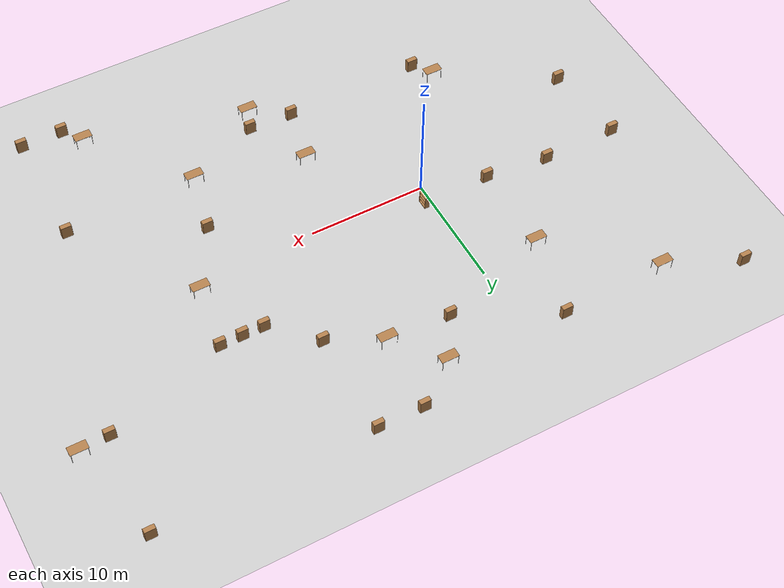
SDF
<sdf version="1.7">
 <world name="default">
  <light name="sun" type="directional">
   <cast_shadows>0</cast_shadows>
   <pose>0 0 10 0 -0 0</pose>
   <diffuse>0.8 0.8 0.8 1</diffuse>
   <specular>0.2 0.2 0.2 1</specular>
   <attenuation>
    <range>1000</range>
    <constant>0.9</constant>
    <linear>0.01</linear>
    <quadratic>0.001</quadratic>
   </attenuation>
   <direction>-0.5 0.1 -0.9</direction>
   <spot><inner_angle>0</inner_angle><outer_angle>0</outer_angle><falloff>0</falloff></spot>
  </light>
  <model name="ground_plane">
   <static>1</static>
   <link name="link">
    <collision name="collision">
     <geometry><plane><normal>0 0 1</normal><size>1000 1000</size></plane></geometry>
     <surface>
      <contact><collide_bitmask>65535</collide_bitmask></contact>
      <friction><ode><mu>100</mu><mu2>50</mu2></ode></friction>
     </surface>
    </collision>
    <visual name="visual">
     <cast_shadows>0</cast_shadows>
     <geometry><plane><normal>0 0 1</normal><size>100 100</size></plane></geometry>
     <material>
      <script><uri>file://media/materials/scripts/gazebo.material</uri><name>Gazebo/Grey</name></script>
     </material>
    </visual>
   </link>
  </model>
  <gravity>0 0 -9.8</gravity>
  <physics type="ode">
   <max_step_size>0.001</max_step_size>
   <real_time_factor>1</real_time_factor>
   <real_time_update_rate>1000</real_time_update_rate>
  </physics>
  <scene>
   <ambient>0.4 0.4 0.4 1</ambient>
   <background>0.7 0.7 0.7 1</background>
   <shadows>0</shadows>
   <origin_visual>0</origin_visual>
  </scene>
  <audio><device>default</device></audio>
  <spherical_coordinates>
   <surface_model>EARTH_WGS84</surface_model>
   <latitude_deg>0</latitude_deg>
   <longitude_deg>0</longitude_deg>
   <elevation>0</elevation>
   <heading_deg>0</heading_deg>
  </spherical_coordinates>
  <model name="bookshelf">
   <static>1</static>
   <link name="link">
    <inertial><mass>1</mass></inertial>
    <visual name="visual1">
     <pose>0 0.005 0.6 0 -0 0</pose>
     <geometry><box><size>0.9 0.01 1.2</size></box></geometry>
     <material>
      <script><uri>file://media/materials/scripts/gazebo.material</uri><name>Gazebo/Wood</name></script>
     </material>
    </visual>
    <visual name="visual2">
     <pose>0.45 -0.195 0.6 0 -0 0</pose>
     <geometry><box><size>0.02 0.4 1.2</size></box></geometry>
     <material>
      <script><uri>file://media/materials/scripts/gazebo.material</uri><name>Gazebo/Wood</name></script>
     </material>
    </visual>
    <visual name="visual3">
     <pose>-0.45 -0.195 0.6 0 -0 0</pose>
     <geometry><box><size>0.02 0.4 1.2</size></box></geometry>
     <material>
      <script><uri>file://media/materials/scripts/gazebo.material</uri><name>Gazebo/Wood</name></script>
     </material>
    </visual>
    <visual name="visual4">
     <pose>0 -0.195 0.03 0 -0 0</pose>
     <geometry><box><size>0.88 0.4 0.06</size></box></geometry>
     <material>
      <script><uri>file://media/materials/scripts/gazebo.material</uri><name>Gazebo/Wood</name></script>
     </material>
    </visual>
    <visual name="visual5">
     <pose>0 -0.195 1.19 0 -0 0</pose>
     <geometry><box><size>0.88 0.4 0.02</size></box></geometry>
     <material>
      <script><uri>file://media/materials/scripts/gazebo.material</uri><name>Gazebo/Wood</name></script>
     </material>
    </visual>
    <visual name="visual6">
     <pose>0 -0.195 0.43 0 -0 0</pose>
     <geometry><box><size>0.88 0.4 0.02</size></box></geometry>
     <material>
      <script><uri>file://media/materials/scripts/gazebo.material</uri><name>Gazebo/Wood</name></script>
     </material>
    </visual>
    <visual name="visual7">
     <pose>0 -0.195 0.8 0 -0 0</pose>
     <geometry><box><size>0.88 0.4 0.02</size></box></geometry>
     <material>
      <script><uri>file://media/materials/scripts/gazebo.material</uri><name>Gazebo/Wood</name></script>
     </material>
    </visual>
   </link>
   <pose>0.43 1.58 0 0 -0 1.57611</pose>
  </model>
  <magnetic_field>6e-06 2.3e-05 -4.2e-05</magnetic_field>
  <atmosphere type="adiabatic"/>
  <plugin name="gazebo_ros_state" filename="libgazebo_ros_state.so">
   <ros><namespace>/gazebo</namespace></ros>
   <update_rate>1.0</update_rate>
  </plugin>
  <model name="bookshelf_0">
   <static>1</static>
   <link name="link">
    <inertial><mass>1</mass></inertial>
    <collision name="back">
     <pose>0 0.005 0.6 0 -0 0</pose>
     <geometry><box><size>0.9 0.01 1.2</size></box></geometry>
    </collision>
    <visual name="visual1">
     <pose>0 0.005 0.6 0 -0 0</pose>
     <geometry><box><size>0.9 0.01 1.2</size></box></geometry>
     <material>
      <script><uri>file://media/materials/scripts/gazebo.material</uri><name>Gazebo/Wood</name></script>
     </material>
    </visual>
    <collision name="left_side">
     <pose>0.45 -0.195 0.6 0 -0 0</pose>
     <geometry><box><size>0.02 0.4 1.2</size></box></geometry>
    </collision>
    <visual name="visual2">
     <pose>0.45 -0.195 0.6 0 -0 0</pose>
     <geometry><box><size>0.02 0.4 1.2</size></box></geometry>
     <material>
      <script><uri>file://media/materials/scripts/gazebo.material</uri><name>Gazebo/Wood</name></script>
     </material>
    </visual>
    <collision name="right_side">
     <pose>-0.45 -0.195 0.6 0 -0 0</pose>
     <geometry><box><size>0.02 0.4 1.2</size></box></geometry>
    </collision>
    <visual name="visual3">
     <pose>-0.45 -0.195 0.6 0 -0 0</pose>
     <geometry><box><size>0.02 0.4 1.2</size></box></geometry>
     <material>
      <script><uri>file://media/materials/scripts/gazebo.material</uri><name>Gazebo/Wood</name></script>
     </material>
    </visual>
    <collision name="bottom">
     <pose>0 -0.195 0.03 0 -0 0</pose>
     <geometry><box><size>0.88 0.4 0.06</size></box></geometry>
    </collision>
    <visual name="visual4">
     <pose>0 -0.195 0.03 0 -0 0</pose>
     <geometry><box><size>0.88 0.4 0.06</size></box></geometry>
     <material>
      <script><uri>file://media/materials/scripts/gazebo.material</uri><name>Gazebo/Wood</name></script>
     </material>
    </visual>
    <collision name="top">
     <pose>0 -0.195 1.19 0 -0 0</pose>
     <geometry><box><size>0.88 0.4 0.02</size></box></geometry>
    </collision>
    <visual name="visual5">
     <pose>0 -0.195 1.19 0 -0 0</pose>
     <geometry><box><size>0.88 0.4 0.02</size></box></geometry>
     <material>
      <script><uri>file://media/materials/scripts/gazebo.material</uri><name>Gazebo/Wood</name></script>
     </material>
    </visual>
    <collision name="low_shelf">
     <pose>0 -0.195 0.43 0 -0 0</pose>
     <geometry><box><size>0.88 0.4 0.02</size></box></geometry>
    </collision>
    <visual name="visual6">
     <pose>0 -0.195 0.43 0 -0 0</pose>
     <geometry><box><size>0.88 0.4 0.02</size></box></geometry>
     <material>
      <script><uri>file://media/materials/scripts/gazebo.material</uri><name>Gazebo/Wood</name></script>
     </material>
    </visual>
    <collision name="high_shelf">
     <pose>0 -0.195 0.8 0 -0 0</pose>
     <geometry><box><size>0.88 0.4 0.02</size></box></geometry>
    </collision>
    <visual name="visual7">
     <pose>0 -0.195 0.8 0 -0 0</pose>
     <geometry><box><size>0.88 0.4 0.02</size></box></geometry>
     <material>
      <script><uri>file://media/materials/scripts/gazebo.material</uri><name>Gazebo/Wood</name></script>
     </material>
    </visual>
   </link>
   <pose>-5.16677 1.95844 0 0 -0 0</pose>
  </model>
  <model name="bookshelf_1">
   <static>1</static>
   <link name="link">
    <inertial><mass>1</mass></inertial>
    <collision name="back">
     <pose>0 0.005 0.6 0 -0 0</pose>
     <geometry><box><size>0.9 0.01 1.2</size></box></geometry>
    </collision>
    <visual name="visual1">
     <pose>0 0.005 0.6 0 -0 0</pose>
     <geometry><box><size>0.9 0.01 1.2</size></box></geometry>
     <material>
      <script><uri>file://media/materials/scripts/gazebo.material</uri><name>Gazebo/Wood</name></script>
     </material>
    </visual>
    <collision name="left_side">
     <pose>0.45 -0.195 0.6 0 -0 0</pose>
     <geometry><box><size>0.02 0.4 1.2</size></box></geometry>
    </collision>
    <visual name="visual2">
     <pose>0.45 -0.195 0.6 0 -0 0</pose>
     <geometry><box><size>0.02 0.4 1.2</size></box></geometry>
     <material>
      <script><uri>file://media/materials/scripts/gazebo.material</uri><name>Gazebo/Wood</name></script>
     </material>
    </visual>
    <collision name="right_side">
     <pose>-0.45 -0.195 0.6 0 -0 0</pose>
     <geometry><box><size>0.02 0.4 1.2</size></box></geometry>
    </collision>
    <visual name="visual3">
     <pose>-0.45 -0.195 0.6 0 -0 0</pose>
     <geometry><box><size>0.02 0.4 1.2</size></box></geometry>
     <material>
      <script><uri>file://media/materials/scripts/gazebo.material</uri><name>Gazebo/Wood</name></script>
     </material>
    </visual>
    <collision name="bottom">
     <pose>0 -0.195 0.03 0 -0 0</pose>
     <geometry><box><size>0.88 0.4 0.06</size></box></geometry>
    </collision>
    <visual name="visual4">
     <pose>0 -0.195 0.03 0 -0 0</pose>
     <geometry><box><size>0.88 0.4 0.06</size></box></geometry>
     <material>
      <script><uri>file://media/materials/scripts/gazebo.material</uri><name>Gazebo/Wood</name></script>
     </material>
    </visual>
    <collision name="top">
     <pose>0 -0.195 1.19 0 -0 0</pose>
     <geometry><box><size>0.88 0.4 0.02</size></box></geometry>
    </collision>
    <visual name="visual5">
     <pose>0 -0.195 1.19 0 -0 0</pose>
     <geometry><box><size>0.88 0.4 0.02</size></box></geometry>
     <material>
      <script><uri>file://media/materials/scripts/gazebo.material</uri><name>Gazebo/Wood</name></script>
     </material>
    </visual>
    <collision name="low_shelf">
     <pose>0 -0.195 0.43 0 -0 0</pose>
     <geometry><box><size>0.88 0.4 0.02</size></box></geometry>
    </collision>
    <visual name="visual6">
     <pose>0 -0.195 0.43 0 -0 0</pose>
     <geometry><box><size>0.88 0.4 0.02</size></box></geometry>
     <material>
      <script><uri>file://media/materials/scripts/gazebo.material</uri><name>Gazebo/Wood</name></script>
     </material>
    </visual>
    <collision name="high_shelf">
     <pose>0 -0.195 0.8 0 -0 0</pose>
     <geometry><box><size>0.88 0.4 0.02</size></box></geometry>
    </collision>
    <visual name="visual7">
     <pose>0 -0.195 0.8 0 -0 0</pose>
     <geometry><box><size>0.88 0.4 0.02</size></box></geometry>
     <material>
      <script><uri>file://media/materials/scripts/gazebo.material</uri><name>Gazebo/Wood</name></script>
     </material>
    </visual>
   </link>
   <pose>-3.48744 16.5909 0 0 -0 0</pose>
  </model>
  <model name="bookshelf_2">
   <static>1</static>
   <link name="link">
    <inertial><mass>1</mass></inertial>
    <collision name="back">
     <pose>0 0.005 0.6 0 -0 0</pose>
     <geometry><box><size>0.9 0.01 1.2</size></box></geometry>
    </collision>
    <visual name="visual1">
     <pose>0 0.005 0.6 0 -0 0</pose>
     <geometry><box><size>0.9 0.01 1.2</size></box></geometry>
     <material>
      <script><uri>file://media/materials/scripts/gazebo.material</uri><name>Gazebo/Wood</name></script>
     </material>
    </visual>
    <collision name="left_side">
     <pose>0.45 -0.195 0.6 0 -0 0</pose>
     <geometry><box><size>0.02 0.4 1.2</size></box></geometry>
    </collision>
    <visual name="visual2">
     <pose>0.45 -0.195 0.6 0 -0 0</pose>
     <geometry><box><size>0.02 0.4 1.2</size></box></geometry>
     <material>
      <script><uri>file://media/materials/scripts/gazebo.material</uri><name>Gazebo/Wood</name></script>
     </material>
    </visual>
    <collision name="right_side">
     <pose>-0.45 -0.195 0.6 0 -0 0</pose>
     <geometry><box><size>0.02 0.4 1.2</size></box></geometry>
    </collision>
    <visual name="visual3">
     <pose>-0.45 -0.195 0.6 0 -0 0</pose>
     <geometry><box><size>0.02 0.4 1.2</size></box></geometry>
     <material>
      <script><uri>file://media/materials/scripts/gazebo.material</uri><name>Gazebo/Wood</name></script>
     </material>
    </visual>
    <collision name="bottom">
     <pose>0 -0.195 0.03 0 -0 0</pose>
     <geometry><box><size>0.88 0.4 0.06</size></box></geometry>
    </collision>
    <visual name="visual4">
     <pose>0 -0.195 0.03 0 -0 0</pose>
     <geometry><box><size>0.88 0.4 0.06</size></box></geometry>
     <material>
      <script><uri>file://media/materials/scripts/gazebo.material</uri><name>Gazebo/Wood</name></script>
     </material>
    </visual>
    <collision name="top">
     <pose>0 -0.195 1.19 0 -0 0</pose>
     <geometry><box><size>0.88 0.4 0.02</size></box></geometry>
    </collision>
    <visual name="visual5">
     <pose>0 -0.195 1.19 0 -0 0</pose>
     <geometry><box><size>0.88 0.4 0.02</size></box></geometry>
     <material>
      <script><uri>file://media/materials/scripts/gazebo.material</uri><name>Gazebo/Wood</name></script>
     </material>
    </visual>
    <collision name="low_shelf">
     <pose>0 -0.195 0.43 0 -0 0</pose>
     <geometry><box><size>0.88 0.4 0.02</size></box></geometry>
    </collision>
    <visual name="visual6">
     <pose>0 -0.195 0.43 0 -0 0</pose>
     <geometry><box><size>0.88 0.4 0.02</size></box></geometry>
     <material>
      <script><uri>file://media/materials/scripts/gazebo.material</uri><name>Gazebo/Wood</name></script>
     </material>
    </visual>
    <collision name="high_shelf">
     <pose>0 -0.195 0.8 0 -0 0</pose>
     <geometry><box><size>0.88 0.4 0.02</size></box></geometry>
    </collision>
    <visual name="visual7">
     <pose>0 -0.195 0.8 0 -0 0</pose>
     <geometry><box><size>0.88 0.4 0.02</size></box></geometry>
     <material>
      <script><uri>file://media/materials/scripts/gazebo.material</uri><name>Gazebo/Wood</name></script>
     </material>
    </visual>
   </link>
   <pose>-10.5688 2.57533 0 0 -0 0</pose>
  </model>
  <model name="table">
   <static>1</static>
   <link name="link">
    <collision name="surface">
     <pose>0 0 1 0 -0 0</pose>
     <geometry><box><size>1.5 0.8 0.03</size></box></geometry>
     <surface><friction><ode><mu>0.6</mu><mu2>0.6</mu2></ode></friction></surface>
    </collision>
    <visual name="visual1">
     <pose>0 0 1 0 -0 0</pose>
     <geometry><box><size>1.5 0.8 0.03</size></box></geometry>
     <material>
      <script><uri>file://media/materials/scripts/gazebo.material</uri><name>Gazebo/Wood</name></script>
     </material>
    </visual>
    <collision name="front_left_leg">
     <pose>0.68 0.38 0.5 0 -0 0</pose>
     <geometry><cylinder><radius>0.02</radius><length>1</length></cylinder></geometry>
    </collision>
    <visual name="front_left_leg">
     <pose>0.68 0.38 0.5 0 -0 0</pose>
     <geometry><cylinder><radius>0.02</radius><length>1</length></cylinder></geometry>
     <material>
      <script><uri>file://media/materials/scripts/gazebo.material</uri><name>Gazebo/Grey</name></script>
     </material>
    </visual>
    <collision name="front_right_leg">
     <pose>0.68 -0.38 0.5 0 -0 0</pose>
     <geometry><cylinder><radius>0.02</radius><length>1</length></cylinder></geometry>
    </collision>
    <visual name="front_right_leg">
     <pose>0.68 -0.38 0.5 0 -0 0</pose>
     <geometry><cylinder><radius>0.02</radius><length>1</length></cylinder></geometry>
     <material>
      <script><uri>file://media/materials/scripts/gazebo.material</uri><name>Gazebo/Grey</name></script>
     </material>
    </visual>
    <collision name="back_right_leg">
     <pose>-0.68 -0.38 0.5 0 -0 0</pose>
     <geometry><cylinder><radius>0.02</radius><length>1</length></cylinder></geometry>
    </collision>
    <visual name="back_right_leg">
     <pose>-0.68 -0.38 0.5 0 -0 0</pose>
     <geometry><cylinder><radius>0.02</radius><length>1</length></cylinder></geometry>
     <material>
      <script><uri>file://media/materials/scripts/gazebo.material</uri><name>Gazebo/Grey</name></script>
     </material>
    </visual>
    <collision name="back_left_leg">
     <pose>-0.68 0.38 0.5 0 -0 0</pose>
     <geometry><cylinder><radius>0.02</radius><length>1</length></cylinder></geometry>
    </collision>
    <visual name="back_left_leg">
     <pose>-0.68 0.38 0.5 0 -0 0</pose>
     <geometry><cylinder><radius>0.02</radius><length>1</length></cylinder></geometry>
     <material>
      <script><uri>file://media/materials/scripts/gazebo.material</uri><name>Gazebo/Grey</name></script>
     </material>
    </visual>
   </link>
   <pose>-5.13257 9.38129 0 0 -0 0</pose>
  </model>
  <light name="user_point_light_0" type="point">
   <pose>-5.13257 9.44358 1 0 -0 0</pose>
   <diffuse>0.5 0.5 0.5 1</diffuse>
   <specular>0.1 0.1 0.1 1</specular>
   <attenuation>
    <range>20</range>
    <constant>0.5</constant>
    <linear>0.01</linear>
    <quadratic>0.001</quadratic>
   </attenuation>
   <cast_shadows>0</cast_shadows>
   <direction>0 0 -1</direction>
  </light>
  <light name="user_point_light_1" type="point">
   <pose>20.3368 1.42781 1 0 -0 0</pose>
   <diffuse>0.5 0.5 0.5 1</diffuse>
   <specular>0.1 0.1 0.1 1</specular>
   <attenuation>
    <range>20</range>
    <constant>0.5</constant>
    <linear>0.01</linear>
    <quadratic>0.001</quadratic>
   </attenuation>
   <cast_shadows>0</cast_shadows>
   <direction>0 0 -1</direction>
  </light>
  <model name="table_0">
   <static>1</static>
   <link name="link">
    <collision name="surface">
     <pose>0 0 1 0 -0 0</pose>
     <geometry><box><size>1.5 0.8 0.03</size></box></geometry>
     <surface><friction><ode><mu>0.6</mu><mu2>0.6</mu2></ode></friction></surface>
    </collision>
    <visual name="visual1">
     <pose>0 0 1 0 -0 0</pose>
     <geometry><box><size>1.5 0.8 0.03</size></box></geometry>
     <material>
      <script><uri>file://media/materials/scripts/gazebo.material</uri><name>Gazebo/Wood</name></script>
     </material>
    </visual>
    <collision name="front_left_leg">
     <pose>0.68 0.38 0.5 0 -0 0</pose>
     <geometry><cylinder><radius>0.02</radius><length>1</length></cylinder></geometry>
    </collision>
    <visual name="front_left_leg">
     <pose>0.68 0.38 0.5 0 -0 0</pose>
     <geometry><cylinder><radius>0.02</radius><length>1</length></cylinder></geometry>
     <material>
      <script><uri>file://media/materials/scripts/gazebo.material</uri><name>Gazebo/Grey</name></script>
     </material>
    </visual>
    <collision name="front_right_leg">
     <pose>0.68 -0.38 0.5 0 -0 0</pose>
     <geometry><cylinder><radius>0.02</radius><length>1</length></cylinder></geometry>
    </collision>
    <visual name="front_right_leg">
     <pose>0.68 -0.38 0.5 0 -0 0</pose>
     <geometry><cylinder><radius>0.02</radius><length>1</length></cylinder></geometry>
     <material>
      <script><uri>file://media/materials/scripts/gazebo.material</uri><name>Gazebo/Grey</name></script>
     </material>
    </visual>
    <collision name="back_right_leg">
     <pose>-0.68 -0.38 0.5 0 -0 0</pose>
     <geometry><cylinder><radius>0.02</radius><length>1</length></cylinder></geometry>
    </collision>
    <visual name="back_right_leg">
     <pose>-0.68 -0.38 0.5 0 -0 0</pose>
     <geometry><cylinder><radius>0.02</radius><length>1</length></cylinder></geometry>
     <material>
      <script><uri>file://media/materials/scripts/gazebo.material</uri><name>Gazebo/Grey</name></script>
     </material>
    </visual>
    <collision name="back_left_leg">
     <pose>-0.68 0.38 0.5 0 -0 0</pose>
     <geometry><cylinder><radius>0.02</radius><length>1</length></cylinder></geometry>
    </collision>
    <visual name="back_left_leg">
     <pose>-0.68 0.38 0.5 0 -0 0</pose>
     <geometry><cylinder><radius>0.02</radius><length>1</length></cylinder></geometry>
     <material>
      <script><uri>file://media/materials/scripts/gazebo.material</uri><name>Gazebo/Grey</name></script>
     </material>
    </visual>
   </link>
   <pose>6.91808 -7.19797 0 0 -0 0</pose>
  </model>
  <model name="bookshelf_3">
   <static>1</static>
   <link name="link">
    <inertial><mass>1</mass></inertial>
    <collision name="back">
     <pose>0 0.005 0.6 0 -0 0</pose>
     <geometry><box><size>0.9 0.01 1.2</size></box></geometry>
    </collision>
    <visual name="visual1">
     <pose>0 0.005 0.6 0 -0 0</pose>
     <geometry><box><size>0.9 0.01 1.2</size></box></geometry>
     <material>
      <script><uri>file://media/materials/scripts/gazebo.material</uri><name>Gazebo/Wood</name></script>
     </material>
    </visual>
    <collision name="left_side">
     <pose>0.45 -0.195 0.6 0 -0 0</pose>
     <geometry><box><size>0.02 0.4 1.2</size></box></geometry>
    </collision>
    <visual name="visual2">
     <pose>0.45 -0.195 0.6 0 -0 0</pose>
     <geometry><box><size>0.02 0.4 1.2</size></box></geometry>
     <material>
      <script><uri>file://media/materials/scripts/gazebo.material</uri><name>Gazebo/Wood</name></script>
     </material>
    </visual>
    <collision name="right_side">
     <pose>-0.45 -0.195 0.6 0 -0 0</pose>
     <geometry><box><size>0.02 0.4 1.2</size></box></geometry>
    </collision>
    <visual name="visual3">
     <pose>-0.45 -0.195 0.6 0 -0 0</pose>
     <geometry><box><size>0.02 0.4 1.2</size></box></geometry>
     <material>
      <script><uri>file://media/materials/scripts/gazebo.material</uri><name>Gazebo/Wood</name></script>
     </material>
    </visual>
    <collision name="bottom">
     <pose>0 -0.195 0.03 0 -0 0</pose>
     <geometry><box><size>0.88 0.4 0.06</size></box></geometry>
    </collision>
    <visual name="visual4">
     <pose>0 -0.195 0.03 0 -0 0</pose>
     <geometry><box><size>0.88 0.4 0.06</size></box></geometry>
     <material>
      <script><uri>file://media/materials/scripts/gazebo.material</uri><name>Gazebo/Wood</name></script>
     </material>
    </visual>
    <collision name="top">
     <pose>0 -0.195 1.19 0 -0 0</pose>
     <geometry><box><size>0.88 0.4 0.02</size></box></geometry>
    </collision>
    <visual name="visual5">
     <pose>0 -0.195 1.19 0 -0 0</pose>
     <geometry><box><size>0.88 0.4 0.02</size></box></geometry>
     <material>
      <script><uri>file://media/materials/scripts/gazebo.material</uri><name>Gazebo/Wood</name></script>
     </material>
    </visual>
    <collision name="low_shelf">
     <pose>0 -0.195 0.43 0 -0 0</pose>
     <geometry><box><size>0.88 0.4 0.02</size></box></geometry>
    </collision>
    <visual name="visual6">
     <pose>0 -0.195 0.43 0 -0 0</pose>
     <geometry><box><size>0.88 0.4 0.02</size></box></geometry>
     <material>
      <script><uri>file://media/materials/scripts/gazebo.material</uri><name>Gazebo/Wood</name></script>
     </material>
    </visual>
    <collision name="high_shelf">
     <pose>0 -0.195 0.8 0 -0 0</pose>
     <geometry><box><size>0.88 0.4 0.02</size></box></geometry>
    </collision>
    <visual name="visual7">
     <pose>0 -0.195 0.8 0 -0 0</pose>
     <geometry><box><size>0.88 0.4 0.02</size></box></geometry>
     <material>
      <script><uri>file://media/materials/scripts/gazebo.material</uri><name>Gazebo/Wood</name></script>
     </material>
    </visual>
   </link>
   <pose>5.82048 -11.903 0 0 -0 0</pose>
  </model>
  <model name="table_1">
   <static>1</static>
   <link name="link">
    <collision name="surface">
     <pose>0 0 1 0 -0 0</pose>
     <geometry><box><size>1.5 0.8 0.03</size></box></geometry>
     <surface><friction><ode><mu>0.6</mu><mu2>0.6</mu2></ode></friction></surface>
    </collision>
    <visual name="visual1">
     <pose>0 0 1 0 -0 0</pose>
     <geometry><box><size>1.5 0.8 0.03</size></box></geometry>
     <material>
      <script><uri>file://media/materials/scripts/gazebo.material</uri><name>Gazebo/Wood</name></script>
     </material>
    </visual>
    <collision name="front_left_leg">
     <pose>0.68 0.38 0.5 0 -0 0</pose>
     <geometry><cylinder><radius>0.02</radius><length>1</length></cylinder></geometry>
    </collision>
    <visual name="front_left_leg">
     <pose>0.68 0.38 0.5 0 -0 0</pose>
     <geometry><cylinder><radius>0.02</radius><length>1</length></cylinder></geometry>
     <material>
      <script><uri>file://media/materials/scripts/gazebo.material</uri><name>Gazebo/Grey</name></script>
     </material>
    </visual>
    <collision name="front_right_leg">
     <pose>0.68 -0.38 0.5 0 -0 0</pose>
     <geometry><cylinder><radius>0.02</radius><length>1</length></cylinder></geometry>
    </collision>
    <visual name="front_right_leg">
     <pose>0.68 -0.38 0.5 0 -0 0</pose>
     <geometry><cylinder><radius>0.02</radius><length>1</length></cylinder></geometry>
     <material>
      <script><uri>file://media/materials/scripts/gazebo.material</uri><name>Gazebo/Grey</name></script>
     </material>
    </visual>
    <collision name="back_right_leg">
     <pose>-0.68 -0.38 0.5 0 -0 0</pose>
     <geometry><cylinder><radius>0.02</radius><length>1</length></cylinder></geometry>
    </collision>
    <visual name="back_right_leg">
     <pose>-0.68 -0.38 0.5 0 -0 0</pose>
     <geometry><cylinder><radius>0.02</radius><length>1</length></cylinder></geometry>
     <material>
      <script><uri>file://media/materials/scripts/gazebo.material</uri><name>Gazebo/Grey</name></script>
     </material>
    </visual>
    <collision name="back_left_leg">
     <pose>-0.68 0.38 0.5 0 -0 0</pose>
     <geometry><cylinder><radius>0.02</radius><length>1</length></cylinder></geometry>
    </collision>
    <visual name="back_left_leg">
     <pose>-0.68 0.38 0.5 0 -0 0</pose>
     <geometry><cylinder><radius>0.02</radius><length>1</length></cylinder></geometry>
     <material>
      <script><uri>file://media/materials/scripts/gazebo.material</uri><name>Gazebo/Grey</name></script>
     </material>
    </visual>
   </link>
   <pose>20.2971 1.0302 0 0 -0 0</pose>
  </model>
  <model name="bookshelf_4">
   <static>1</static>
   <link name="link">
    <inertial><mass>1</mass></inertial>
    <collision name="back">
     <pose>0 0.005 0.6 0 -0 0</pose>
     <geometry><box><size>0.9 0.01 1.2</size></box></geometry>
    </collision>
    <visual name="visual1">
     <pose>0 0.005 0.6 0 -0 0</pose>
     <geometry><box><size>0.9 0.01 1.2</size></box></geometry>
     <material>
      <script><uri>file://media/materials/scripts/gazebo.material</uri><name>Gazebo/Wood</name></script>
     </material>
    </visual>
    <collision name="left_side">
     <pose>0.45 -0.195 0.6 0 -0 0</pose>
     <geometry><box><size>0.02 0.4 1.2</size></box></geometry>
    </collision>
    <visual name="visual2">
     <pose>0.45 -0.195 0.6 0 -0 0</pose>
     <geometry><box><size>0.02 0.4 1.2</size></box></geometry>
     <material>
      <script><uri>file://media/materials/scripts/gazebo.material</uri><name>Gazebo/Wood</name></script>
     </material>
    </visual>
    <collision name="right_side">
     <pose>-0.45 -0.195 0.6 0 -0 0</pose>
     <geometry><box><size>0.02 0.4 1.2</size></box></geometry>
    </collision>
    <visual name="visual3">
     <pose>-0.45 -0.195 0.6 0 -0 0</pose>
     <geometry><box><size>0.02 0.4 1.2</size></box></geometry>
     <material>
      <script><uri>file://media/materials/scripts/gazebo.material</uri><name>Gazebo/Wood</name></script>
     </material>
    </visual>
    <collision name="bottom">
     <pose>0 -0.195 0.03 0 -0 0</pose>
     <geometry><box><size>0.88 0.4 0.06</size></box></geometry>
    </collision>
    <visual name="visual4">
     <pose>0 -0.195 0.03 0 -0 0</pose>
     <geometry><box><size>0.88 0.4 0.06</size></box></geometry>
     <material>
      <script><uri>file://media/materials/scripts/gazebo.material</uri><name>Gazebo/Wood</name></script>
     </material>
    </visual>
    <collision name="top">
     <pose>0 -0.195 1.19 0 -0 0</pose>
     <geometry><box><size>0.88 0.4 0.02</size></box></geometry>
    </collision>
    <visual name="visual5">
     <pose>0 -0.195 1.19 0 -0 0</pose>
     <geometry><box><size>0.88 0.4 0.02</size></box></geometry>
     <material>
      <script><uri>file://media/materials/scripts/gazebo.material</uri><name>Gazebo/Wood</name></script>
     </material>
    </visual>
    <collision name="low_shelf">
     <pose>0 -0.195 0.43 0 -0 0</pose>
     <geometry><box><size>0.88 0.4 0.02</size></box></geometry>
    </collision>
    <visual name="visual6">
     <pose>0 -0.195 0.43 0 -0 0</pose>
     <geometry><box><size>0.88 0.4 0.02</size></box></geometry>
     <material>
      <script><uri>file://media/materials/scripts/gazebo.material</uri><name>Gazebo/Wood</name></script>
     </material>
    </visual>
    <collision name="high_shelf">
     <pose>0 -0.195 0.8 0 -0 0</pose>
     <geometry><box><size>0.88 0.4 0.02</size></box></geometry>
    </collision>
    <visual name="visual7">
     <pose>0 -0.195 0.8 0 -0 0</pose>
     <geometry><box><size>0.88 0.4 0.02</size></box></geometry>
     <material>
      <script><uri>file://media/materials/scripts/gazebo.material</uri><name>Gazebo/Wood</name></script>
     </material>
    </visual>
   </link>
   <pose>17.1921 -4.14453 0 0 -0 0</pose>
  </model>
  <model name="bookshelf_5">
   <static>1</static>
   <link name="link">
    <inertial><mass>1</mass></inertial>
    <collision name="back">
     <pose>0 0.005 0.6 0 -0 0</pose>
     <geometry><box><size>0.9 0.01 1.2</size></box></geometry>
    </collision>
    <visual name="visual1">
     <pose>0 0.005 0.6 0 -0 0</pose>
     <geometry><box><size>0.9 0.01 1.2</size></box></geometry>
     <material>
      <script><uri>file://media/materials/scripts/gazebo.material</uri><name>Gazebo/Wood</name></script>
     </material>
    </visual>
    <collision name="left_side">
     <pose>0.45 -0.195 0.6 0 -0 0</pose>
     <geometry><box><size>0.02 0.4 1.2</size></box></geometry>
    </collision>
    <visual name="visual2">
     <pose>0.45 -0.195 0.6 0 -0 0</pose>
     <geometry><box><size>0.02 0.4 1.2</size></box></geometry>
     <material>
      <script><uri>file://media/materials/scripts/gazebo.material</uri><name>Gazebo/Wood</name></script>
     </material>
    </visual>
    <collision name="right_side">
     <pose>-0.45 -0.195 0.6 0 -0 0</pose>
     <geometry><box><size>0.02 0.4 1.2</size></box></geometry>
    </collision>
    <visual name="visual3">
     <pose>-0.45 -0.195 0.6 0 -0 0</pose>
     <geometry><box><size>0.02 0.4 1.2</size></box></geometry>
     <material>
      <script><uri>file://media/materials/scripts/gazebo.material</uri><name>Gazebo/Wood</name></script>
     </material>
    </visual>
    <collision name="bottom">
     <pose>0 -0.195 0.03 0 -0 0</pose>
     <geometry><box><size>0.88 0.4 0.06</size></box></geometry>
    </collision>
    <visual name="visual4">
     <pose>0 -0.195 0.03 0 -0 0</pose>
     <geometry><box><size>0.88 0.4 0.06</size></box></geometry>
     <material>
      <script><uri>file://media/materials/scripts/gazebo.material</uri><name>Gazebo/Wood</name></script>
     </material>
    </visual>
    <collision name="top">
     <pose>0 -0.195 1.19 0 -0 0</pose>
     <geometry><box><size>0.88 0.4 0.02</size></box></geometry>
    </collision>
    <visual name="visual5">
     <pose>0 -0.195 1.19 0 -0 0</pose>
     <geometry><box><size>0.88 0.4 0.02</size></box></geometry>
     <material>
      <script><uri>file://media/materials/scripts/gazebo.material</uri><name>Gazebo/Wood</name></script>
     </material>
    </visual>
    <collision name="low_shelf">
     <pose>0 -0.195 0.43 0 -0 0</pose>
     <geometry><box><size>0.88 0.4 0.02</size></box></geometry>
    </collision>
    <visual name="visual6">
     <pose>0 -0.195 0.43 0 -0 0</pose>
     <geometry><box><size>0.88 0.4 0.02</size></box></geometry>
     <material>
      <script><uri>file://media/materials/scripts/gazebo.material</uri><name>Gazebo/Wood</name></script>
     </material>
    </visual>
    <collision name="high_shelf">
     <pose>0 -0.195 0.8 0 -0 0</pose>
     <geometry><box><size>0.88 0.4 0.02</size></box></geometry>
    </collision>
    <visual name="visual7">
     <pose>0 -0.195 0.8 0 -0 0</pose>
     <geometry><box><size>0.88 0.4 0.02</size></box></geometry>
     <material>
      <script><uri>file://media/materials/scripts/gazebo.material</uri><name>Gazebo/Wood</name></script>
     </material>
    </visual>
   </link>
   <pose>17.4711 6.68275 0 0 -0 0</pose>
  </model>
  <model name="bookshelf_6">
   <static>1</static>
   <link name="link">
    <inertial><mass>1</mass></inertial>
    <collision name="back">
     <pose>0 0.005 0.6 0 -0 0</pose>
     <geometry><box><size>0.9 0.01 1.2</size></box></geometry>
    </collision>
    <visual name="visual1">
     <pose>0 0.005 0.6 0 -0 0</pose>
     <geometry><box><size>0.9 0.01 1.2</size></box></geometry>
     <material>
      <script><uri>file://media/materials/scripts/gazebo.material</uri><name>Gazebo/Wood</name></script>
     </material>
    </visual>
    <collision name="left_side">
     <pose>0.45 -0.195 0.6 0 -0 0</pose>
     <geometry><box><size>0.02 0.4 1.2</size></box></geometry>
    </collision>
    <visual name="visual2">
     <pose>0.45 -0.195 0.6 0 -0 0</pose>
     <geometry><box><size>0.02 0.4 1.2</size></box></geometry>
     <material>
      <script><uri>file://media/materials/scripts/gazebo.material</uri><name>Gazebo/Wood</name></script>
     </material>
    </visual>
    <collision name="right_side">
     <pose>-0.45 -0.195 0.6 0 -0 0</pose>
     <geometry><box><size>0.02 0.4 1.2</size></box></geometry>
    </collision>
    <visual name="visual3">
     <pose>-0.45 -0.195 0.6 0 -0 0</pose>
     <geometry><box><size>0.02 0.4 1.2</size></box></geometry>
     <material>
      <script><uri>file://media/materials/scripts/gazebo.material</uri><name>Gazebo/Wood</name></script>
     </material>
    </visual>
    <collision name="bottom">
     <pose>0 -0.195 0.03 0 -0 0</pose>
     <geometry><box><size>0.88 0.4 0.06</size></box></geometry>
    </collision>
    <visual name="visual4">
     <pose>0 -0.195 0.03 0 -0 0</pose>
     <geometry><box><size>0.88 0.4 0.06</size></box></geometry>
     <material>
      <script><uri>file://media/materials/scripts/gazebo.material</uri><name>Gazebo/Wood</name></script>
     </material>
    </visual>
    <collision name="top">
     <pose>0 -0.195 1.19 0 -0 0</pose>
     <geometry><box><size>0.88 0.4 0.02</size></box></geometry>
    </collision>
    <visual name="visual5">
     <pose>0 -0.195 1.19 0 -0 0</pose>
     <geometry><box><size>0.88 0.4 0.02</size></box></geometry>
     <material>
      <script><uri>file://media/materials/scripts/gazebo.material</uri><name>Gazebo/Wood</name></script>
     </material>
    </visual>
    <collision name="low_shelf">
     <pose>0 -0.195 0.43 0 -0 0</pose>
     <geometry><box><size>0.88 0.4 0.02</size></box></geometry>
    </collision>
    <visual name="visual6">
     <pose>0 -0.195 0.43 0 -0 0</pose>
     <geometry><box><size>0.88 0.4 0.02</size></box></geometry>
     <material>
      <script><uri>file://media/materials/scripts/gazebo.material</uri><name>Gazebo/Wood</name></script>
     </material>
    </visual>
    <collision name="high_shelf">
     <pose>0 -0.195 0.8 0 -0 0</pose>
     <geometry><box><size>0.88 0.4 0.02</size></box></geometry>
    </collision>
    <visual name="visual7">
     <pose>0 -0.195 0.8 0 -0 0</pose>
     <geometry><box><size>0.88 0.4 0.02</size></box></geometry>
     <material>
      <script><uri>file://media/materials/scripts/gazebo.material</uri><name>Gazebo/Wood</name></script>
     </material>
    </visual>
   </link>
   <pose>21.1726 6.70269 0 0 -0 0</pose>
  </model>
  <model name="bookshelf_7">
   <static>1</static>
   <link name="link">
    <inertial><mass>1</mass></inertial>
    <collision name="back">
     <pose>0 0.005 0.6 0 -0 0</pose>
     <geometry><box><size>0.9 0.01 1.2</size></box></geometry>
    </collision>
    <visual name="visual1">
     <pose>0 0.005 0.6 0 -0 0</pose>
     <geometry><box><size>0.9 0.01 1.2</size></box></geometry>
     <material>
      <script><uri>file://media/materials/scripts/gazebo.material</uri><name>Gazebo/Wood</name></script>
     </material>
    </visual>
    <collision name="left_side">
     <pose>0.45 -0.195 0.6 0 -0 0</pose>
     <geometry><box><size>0.02 0.4 1.2</size></box></geometry>
    </collision>
    <visual name="visual2">
     <pose>0.45 -0.195 0.6 0 -0 0</pose>
     <geometry><box><size>0.02 0.4 1.2</size></box></geometry>
     <material>
      <script><uri>file://media/materials/scripts/gazebo.material</uri><name>Gazebo/Wood</name></script>
     </material>
    </visual>
    <collision name="right_side">
     <pose>-0.45 -0.195 0.6 0 -0 0</pose>
     <geometry><box><size>0.02 0.4 1.2</size></box></geometry>
    </collision>
    <visual name="visual3">
     <pose>-0.45 -0.195 0.6 0 -0 0</pose>
     <geometry><box><size>0.02 0.4 1.2</size></box></geometry>
     <material>
      <script><uri>file://media/materials/scripts/gazebo.material</uri><name>Gazebo/Wood</name></script>
     </material>
    </visual>
    <collision name="bottom">
     <pose>0 -0.195 0.03 0 -0 0</pose>
     <geometry><box><size>0.88 0.4 0.06</size></box></geometry>
    </collision>
    <visual name="visual4">
     <pose>0 -0.195 0.03 0 -0 0</pose>
     <geometry><box><size>0.88 0.4 0.06</size></box></geometry>
     <material>
      <script><uri>file://media/materials/scripts/gazebo.material</uri><name>Gazebo/Wood</name></script>
     </material>
    </visual>
    <collision name="top">
     <pose>0 -0.195 1.19 0 -0 0</pose>
     <geometry><box><size>0.88 0.4 0.02</size></box></geometry>
    </collision>
    <visual name="visual5">
     <pose>0 -0.195 1.19 0 -0 0</pose>
     <geometry><box><size>0.88 0.4 0.02</size></box></geometry>
     <material>
      <script><uri>file://media/materials/scripts/gazebo.material</uri><name>Gazebo/Wood</name></script>
     </material>
    </visual>
    <collision name="low_shelf">
     <pose>0 -0.195 0.43 0 -0 0</pose>
     <geometry><box><size>0.88 0.4 0.02</size></box></geometry>
    </collision>
    <visual name="visual6">
     <pose>0 -0.195 0.43 0 -0 0</pose>
     <geometry><box><size>0.88 0.4 0.02</size></box></geometry>
     <material>
      <script><uri>file://media/materials/scripts/gazebo.material</uri><name>Gazebo/Wood</name></script>
     </material>
    </visual>
    <collision name="high_shelf">
     <pose>0 -0.195 0.8 0 -0 0</pose>
     <geometry><box><size>0.88 0.4 0.02</size></box></geometry>
    </collision>
    <visual name="visual7">
     <pose>0 -0.195 0.8 0 -0 0</pose>
     <geometry><box><size>0.88 0.4 0.02</size></box></geometry>
     <material>
      <script><uri>file://media/materials/scripts/gazebo.material</uri><name>Gazebo/Wood</name></script>
     </material>
    </visual>
   </link>
   <pose>19.2821 6.66288 0 0 -0 0</pose>
  </model>
  <model name="bookshelf_8">
   <static>1</static>
   <link name="link">
    <inertial><mass>1</mass></inertial>
    <collision name="back">
     <pose>0 0.005 0.6 0 -0 0</pose>
     <geometry><box><size>0.9 0.01 1.2</size></box></geometry>
    </collision>
    <visual name="visual1">
     <pose>0 0.005 0.6 0 -0 0</pose>
     <geometry><box><size>0.9 0.01 1.2</size></box></geometry>
     <material>
      <script><uri>file://media/materials/scripts/gazebo.material</uri><name>Gazebo/Wood</name></script>
     </material>
    </visual>
    <collision name="left_side">
     <pose>0.45 -0.195 0.6 0 -0 0</pose>
     <geometry><box><size>0.02 0.4 1.2</size></box></geometry>
    </collision>
    <visual name="visual2">
     <pose>0.45 -0.195 0.6 0 -0 0</pose>
     <geometry><box><size>0.02 0.4 1.2</size></box></geometry>
     <material>
      <script><uri>file://media/materials/scripts/gazebo.material</uri><name>Gazebo/Wood</name></script>
     </material>
    </visual>
    <collision name="right_side">
     <pose>-0.45 -0.195 0.6 0 -0 0</pose>
     <geometry><box><size>0.02 0.4 1.2</size></box></geometry>
    </collision>
    <visual name="visual3">
     <pose>-0.45 -0.195 0.6 0 -0 0</pose>
     <geometry><box><size>0.02 0.4 1.2</size></box></geometry>
     <material>
      <script><uri>file://media/materials/scripts/gazebo.material</uri><name>Gazebo/Wood</name></script>
     </material>
    </visual>
    <collision name="bottom">
     <pose>0 -0.195 0.03 0 -0 0</pose>
     <geometry><box><size>0.88 0.4 0.06</size></box></geometry>
    </collision>
    <visual name="visual4">
     <pose>0 -0.195 0.03 0 -0 0</pose>
     <geometry><box><size>0.88 0.4 0.06</size></box></geometry>
     <material>
      <script><uri>file://media/materials/scripts/gazebo.material</uri><name>Gazebo/Wood</name></script>
     </material>
    </visual>
    <collision name="top">
     <pose>0 -0.195 1.19 0 -0 0</pose>
     <geometry><box><size>0.88 0.4 0.02</size></box></geometry>
    </collision>
    <visual name="visual5">
     <pose>0 -0.195 1.19 0 -0 0</pose>
     <geometry><box><size>0.88 0.4 0.02</size></box></geometry>
     <material>
      <script><uri>file://media/materials/scripts/gazebo.material</uri><name>Gazebo/Wood</name></script>
     </material>
    </visual>
    <collision name="low_shelf">
     <pose>0 -0.195 0.43 0 -0 0</pose>
     <geometry><box><size>0.88 0.4 0.02</size></box></geometry>
    </collision>
    <visual name="visual6">
     <pose>0 -0.195 0.43 0 -0 0</pose>
     <geometry><box><size>0.88 0.4 0.02</size></box></geometry>
     <material>
      <script><uri>file://media/materials/scripts/gazebo.material</uri><name>Gazebo/Wood</name></script>
     </material>
    </visual>
    <collision name="high_shelf">
     <pose>0 -0.195 0.8 0 -0 0</pose>
     <geometry><box><size>0.88 0.4 0.02</size></box></geometry>
    </collision>
    <visual name="visual7">
     <pose>0 -0.195 0.8 0 -0 0</pose>
     <geometry><box><size>0.88 0.4 0.02</size></box></geometry>
     <material>
      <script><uri>file://media/materials/scripts/gazebo.material</uri><name>Gazebo/Wood</name></script>
     </material>
    </visual>
   </link>
   <pose>14.1199 18.7319 0 0 -0 0</pose>
  </model>
  <model name="bookshelf_9">
   <static>1</static>
   <link name="link">
    <inertial><mass>1</mass></inertial>
    <collision name="back">
     <pose>0 0.005 0.6 0 -0 0</pose>
     <geometry><box><size>0.9 0.01 1.2</size></box></geometry>
    </collision>
    <visual name="visual1">
     <pose>0 0.005 0.6 0 -0 0</pose>
     <geometry><box><size>0.9 0.01 1.2</size></box></geometry>
     <material>
      <script><uri>file://media/materials/scripts/gazebo.material</uri><name>Gazebo/Wood</name></script>
     </material>
    </visual>
    <collision name="left_side">
     <pose>0.45 -0.195 0.6 0 -0 0</pose>
     <geometry><box><size>0.02 0.4 1.2</size></box></geometry>
    </collision>
    <visual name="visual2">
     <pose>0.45 -0.195 0.6 0 -0 0</pose>
     <geometry><box><size>0.02 0.4 1.2</size></box></geometry>
     <material>
      <script><uri>file://media/materials/scripts/gazebo.material</uri><name>Gazebo/Wood</name></script>
     </material>
    </visual>
    <collision name="right_side">
     <pose>-0.45 -0.195 0.6 0 -0 0</pose>
     <geometry><box><size>0.02 0.4 1.2</size></box></geometry>
    </collision>
    <visual name="visual3">
     <pose>-0.45 -0.195 0.6 0 -0 0</pose>
     <geometry><box><size>0.02 0.4 1.2</size></box></geometry>
     <material>
      <script><uri>file://media/materials/scripts/gazebo.material</uri><name>Gazebo/Wood</name></script>
     </material>
    </visual>
    <collision name="bottom">
     <pose>0 -0.195 0.03 0 -0 0</pose>
     <geometry><box><size>0.88 0.4 0.06</size></box></geometry>
    </collision>
    <visual name="visual4">
     <pose>0 -0.195 0.03 0 -0 0</pose>
     <geometry><box><size>0.88 0.4 0.06</size></box></geometry>
     <material>
      <script><uri>file://media/materials/scripts/gazebo.material</uri><name>Gazebo/Wood</name></script>
     </material>
    </visual>
    <collision name="top">
     <pose>0 -0.195 1.19 0 -0 0</pose>
     <geometry><box><size>0.88 0.4 0.02</size></box></geometry>
    </collision>
    <visual name="visual5">
     <pose>0 -0.195 1.19 0 -0 0</pose>
     <geometry><box><size>0.88 0.4 0.02</size></box></geometry>
     <material>
      <script><uri>file://media/materials/scripts/gazebo.material</uri><name>Gazebo/Wood</name></script>
     </material>
    </visual>
    <collision name="low_shelf">
     <pose>0 -0.195 0.43 0 -0 0</pose>
     <geometry><box><size>0.88 0.4 0.02</size></box></geometry>
    </collision>
    <visual name="visual6">
     <pose>0 -0.195 0.43 0 -0 0</pose>
     <geometry><box><size>0.88 0.4 0.02</size></box></geometry>
     <material>
      <script><uri>file://media/materials/scripts/gazebo.material</uri><name>Gazebo/Wood</name></script>
     </material>
    </visual>
    <collision name="high_shelf">
     <pose>0 -0.195 0.8 0 -0 0</pose>
     <geometry><box><size>0.88 0.4 0.02</size></box></geometry>
    </collision>
    <visual name="visual7">
     <pose>0 -0.195 0.8 0 -0 0</pose>
     <geometry><box><size>0.88 0.4 0.02</size></box></geometry>
     <material>
      <script><uri>file://media/materials/scripts/gazebo.material</uri><name>Gazebo/Wood</name></script>
     </material>
    </visual>
   </link>
   <pose>14.1396 10.0153 0 0 -0 0</pose>
  </model>
  <model name="bookshelf_10">
   <static>1</static>
   <link name="link">
    <inertial><mass>1</mass></inertial>
    <collision name="back">
     <pose>0 0.005 0.6 0 -0 0</pose>
     <geometry><box><size>0.9 0.01 1.2</size></box></geometry>
    </collision>
    <visual name="visual1">
     <pose>0 0.005 0.6 0 -0 0</pose>
     <geometry><box><size>0.9 0.01 1.2</size></box></geometry>
     <material>
      <script><uri>file://media/materials/scripts/gazebo.material</uri><name>Gazebo/Wood</name></script>
     </material>
    </visual>
    <collision name="left_side">
     <pose>0.45 -0.195 0.6 0 -0 0</pose>
     <geometry><box><size>0.02 0.4 1.2</size></box></geometry>
    </collision>
    <visual name="visual2">
     <pose>0.45 -0.195 0.6 0 -0 0</pose>
     <geometry><box><size>0.02 0.4 1.2</size></box></geometry>
     <material>
      <script><uri>file://media/materials/scripts/gazebo.material</uri><name>Gazebo/Wood</name></script>
     </material>
    </visual>
    <collision name="right_side">
     <pose>-0.45 -0.195 0.6 0 -0 0</pose>
     <geometry><box><size>0.02 0.4 1.2</size></box></geometry>
    </collision>
    <visual name="visual3">
     <pose>-0.45 -0.195 0.6 0 -0 0</pose>
     <geometry><box><size>0.02 0.4 1.2</size></box></geometry>
     <material>
      <script><uri>file://media/materials/scripts/gazebo.material</uri><name>Gazebo/Wood</name></script>
     </material>
    </visual>
    <collision name="bottom">
     <pose>0 -0.195 0.03 0 -0 0</pose>
     <geometry><box><size>0.88 0.4 0.06</size></box></geometry>
    </collision>
    <visual name="visual4">
     <pose>0 -0.195 0.03 0 -0 0</pose>
     <geometry><box><size>0.88 0.4 0.06</size></box></geometry>
     <material>
      <script><uri>file://media/materials/scripts/gazebo.material</uri><name>Gazebo/Wood</name></script>
     </material>
    </visual>
    <collision name="top">
     <pose>0 -0.195 1.19 0 -0 0</pose>
     <geometry><box><size>0.88 0.4 0.02</size></box></geometry>
    </collision>
    <visual name="visual5">
     <pose>0 -0.195 1.19 0 -0 0</pose>
     <geometry><box><size>0.88 0.4 0.02</size></box></geometry>
     <material>
      <script><uri>file://media/materials/scripts/gazebo.material</uri><name>Gazebo/Wood</name></script>
     </material>
    </visual>
    <collision name="low_shelf">
     <pose>0 -0.195 0.43 0 -0 0</pose>
     <geometry><box><size>0.88 0.4 0.02</size></box></geometry>
    </collision>
    <visual name="visual6">
     <pose>0 -0.195 0.43 0 -0 0</pose>
     <geometry><box><size>0.88 0.4 0.02</size></box></geometry>
     <material>
      <script><uri>file://media/materials/scripts/gazebo.material</uri><name>Gazebo/Wood</name></script>
     </material>
    </visual>
    <collision name="high_shelf">
     <pose>0 -0.195 0.8 0 -0 0</pose>
     <geometry><box><size>0.88 0.4 0.02</size></box></geometry>
    </collision>
    <visual name="visual7">
     <pose>0 -0.195 0.8 0 -0 0</pose>
     <geometry><box><size>0.88 0.4 0.02</size></box></geometry>
     <material>
      <script><uri>file://media/materials/scripts/gazebo.material</uri><name>Gazebo/Wood</name></script>
     </material>
    </visual>
   </link>
   <pose>32.164 18.7319 0 0 -0 0</pose>
  </model>
  <model name="bookshelf_11">
   <static>1</static>
   <link name="link">
    <inertial><mass>1</mass></inertial>
    <collision name="back">
     <pose>0 0.005 0.6 0 -0 0</pose>
     <geometry><box><size>0.9 0.01 1.2</size></box></geometry>
    </collision>
    <visual name="visual1">
     <pose>0 0.005 0.6 0 -0 0</pose>
     <geometry><box><size>0.9 0.01 1.2</size></box></geometry>
     <material>
      <script><uri>file://media/materials/scripts/gazebo.material</uri><name>Gazebo/Wood</name></script>
     </material>
    </visual>
    <collision name="left_side">
     <pose>0.45 -0.195 0.6 0 -0 0</pose>
     <geometry><box><size>0.02 0.4 1.2</size></box></geometry>
    </collision>
    <visual name="visual2">
     <pose>0.45 -0.195 0.6 0 -0 0</pose>
     <geometry><box><size>0.02 0.4 1.2</size></box></geometry>
     <material>
      <script><uri>file://media/materials/scripts/gazebo.material</uri><name>Gazebo/Wood</name></script>
     </material>
    </visual>
    <collision name="right_side">
     <pose>-0.45 -0.195 0.6 0 -0 0</pose>
     <geometry><box><size>0.02 0.4 1.2</size></box></geometry>
    </collision>
    <visual name="visual3">
     <pose>-0.45 -0.195 0.6 0 -0 0</pose>
     <geometry><box><size>0.02 0.4 1.2</size></box></geometry>
     <material>
      <script><uri>file://media/materials/scripts/gazebo.material</uri><name>Gazebo/Wood</name></script>
     </material>
    </visual>
    <collision name="bottom">
     <pose>0 -0.195 0.03 0 -0 0</pose>
     <geometry><box><size>0.88 0.4 0.06</size></box></geometry>
    </collision>
    <visual name="visual4">
     <pose>0 -0.195 0.03 0 -0 0</pose>
     <geometry><box><size>0.88 0.4 0.06</size></box></geometry>
     <material>
      <script><uri>file://media/materials/scripts/gazebo.material</uri><name>Gazebo/Wood</name></script>
     </material>
    </visual>
    <collision name="top">
     <pose>0 -0.195 1.19 0 -0 0</pose>
     <geometry><box><size>0.88 0.4 0.02</size></box></geometry>
    </collision>
    <visual name="visual5">
     <pose>0 -0.195 1.19 0 -0 0</pose>
     <geometry><box><size>0.88 0.4 0.02</size></box></geometry>
     <material>
      <script><uri>file://media/materials/scripts/gazebo.material</uri><name>Gazebo/Wood</name></script>
     </material>
    </visual>
    <collision name="low_shelf">
     <pose>0 -0.195 0.43 0 -0 0</pose>
     <geometry><box><size>0.88 0.4 0.02</size></box></geometry>
    </collision>
    <visual name="visual6">
     <pose>0 -0.195 0.43 0 -0 0</pose>
     <geometry><box><size>0.88 0.4 0.02</size></box></geometry>
     <material>
      <script><uri>file://media/materials/scripts/gazebo.material</uri><name>Gazebo/Wood</name></script>
     </material>
    </visual>
    <collision name="high_shelf">
     <pose>0 -0.195 0.8 0 -0 0</pose>
     <geometry><box><size>0.88 0.4 0.02</size></box></geometry>
    </collision>
    <visual name="visual7">
     <pose>0 -0.195 0.8 0 -0 0</pose>
     <geometry><box><size>0.88 0.4 0.02</size></box></geometry>
     <material>
      <script><uri>file://media/materials/scripts/gazebo.material</uri><name>Gazebo/Wood</name></script>
     </material>
    </visual>
   </link>
   <pose>31.5316 10.0153 0 0 -0 0</pose>
  </model>
  <model name="table_2">
   <static>1</static>
   <link name="link">
    <collision name="surface">
     <pose>0 0 1 0 -0 0</pose>
     <geometry><box><size>1.5 0.8 0.03</size></box></geometry>
     <surface><friction><ode><mu>0.6</mu><mu2>0.6</mu2></ode></friction></surface>
    </collision>
    <visual name="visual1">
     <pose>0 0 1 0 -0 0</pose>
     <geometry><box><size>1.5 0.8 0.03</size></box></geometry>
     <material>
      <script><uri>file://media/materials/scripts/gazebo.material</uri><name>Gazebo/Wood</name></script>
     </material>
    </visual>
    <collision name="front_left_leg">
     <pose>0.68 0.38 0.5 0 -0 0</pose>
     <geometry><cylinder><radius>0.02</radius><length>1</length></cylinder></geometry>
    </collision>
    <visual name="front_left_leg">
     <pose>0.68 0.38 0.5 0 -0 0</pose>
     <geometry><cylinder><radius>0.02</radius><length>1</length></cylinder></geometry>
     <material>
      <script><uri>file://media/materials/scripts/gazebo.material</uri><name>Gazebo/Grey</name></script>
     </material>
    </visual>
    <collision name="front_right_leg">
     <pose>0.68 -0.38 0.5 0 -0 0</pose>
     <geometry><cylinder><radius>0.02</radius><length>1</length></cylinder></geometry>
    </collision>
    <visual name="front_right_leg">
     <pose>0.68 -0.38 0.5 0 -0 0</pose>
     <geometry><cylinder><radius>0.02</radius><length>1</length></cylinder></geometry>
     <material>
      <script><uri>file://media/materials/scripts/gazebo.material</uri><name>Gazebo/Grey</name></script>
     </material>
    </visual>
    <collision name="back_right_leg">
     <pose>-0.68 -0.38 0.5 0 -0 0</pose>
     <geometry><cylinder><radius>0.02</radius><length>1</length></cylinder></geometry>
    </collision>
    <visual name="back_right_leg">
     <pose>-0.68 -0.38 0.5 0 -0 0</pose>
     <geometry><cylinder><radius>0.02</radius><length>1</length></cylinder></geometry>
     <material>
      <script><uri>file://media/materials/scripts/gazebo.material</uri><name>Gazebo/Grey</name></script>
     </material>
    </visual>
    <collision name="back_left_leg">
     <pose>-0.68 0.38 0.5 0 -0 0</pose>
     <geometry><cylinder><radius>0.02</radius><length>1</length></cylinder></geometry>
    </collision>
    <visual name="back_left_leg">
     <pose>-0.68 0.38 0.5 0 -0 0</pose>
     <geometry><cylinder><radius>0.02</radius><length>1</length></cylinder></geometry>
     <material>
      <script><uri>file://media/materials/scripts/gazebo.material</uri><name>Gazebo/Grey</name></script>
     </material>
    </visual>
   </link>
   <pose>34.0603 10.0725 0 0 -0 0</pose>
  </model>
  <model name="bookshelf_12">
   <static>1</static>
   <link name="link">
    <inertial><mass>1</mass></inertial>
    <collision name="back">
     <pose>0 0.005 0.6 0 -0 0</pose>
     <geometry><box><size>0.9 0.01 1.2</size></box></geometry>
    </collision>
    <visual name="visual1">
     <pose>0 0.005 0.6 0 -0 0</pose>
     <geometry><box><size>0.9 0.01 1.2</size></box></geometry>
     <material>
      <script><uri>file://media/materials/scripts/gazebo.material</uri><name>Gazebo/Wood</name></script>
     </material>
    </visual>
    <collision name="left_side">
     <pose>0.45 -0.195 0.6 0 -0 0</pose>
     <geometry><box><size>0.02 0.4 1.2</size></box></geometry>
    </collision>
    <visual name="visual2">
     <pose>0.45 -0.195 0.6 0 -0 0</pose>
     <geometry><box><size>0.02 0.4 1.2</size></box></geometry>
     <material>
      <script><uri>file://media/materials/scripts/gazebo.material</uri><name>Gazebo/Wood</name></script>
     </material>
    </visual>
    <collision name="right_side">
     <pose>-0.45 -0.195 0.6 0 -0 0</pose>
     <geometry><box><size>0.02 0.4 1.2</size></box></geometry>
    </collision>
    <visual name="visual3">
     <pose>-0.45 -0.195 0.6 0 -0 0</pose>
     <geometry><box><size>0.02 0.4 1.2</size></box></geometry>
     <material>
      <script><uri>file://media/materials/scripts/gazebo.material</uri><name>Gazebo/Wood</name></script>
     </material>
    </visual>
    <collision name="bottom">
     <pose>0 -0.195 0.03 0 -0 0</pose>
     <geometry><box><size>0.88 0.4 0.06</size></box></geometry>
    </collision>
    <visual name="visual4">
     <pose>0 -0.195 0.03 0 -0 0</pose>
     <geometry><box><size>0.88 0.4 0.06</size></box></geometry>
     <material>
      <script><uri>file://media/materials/scripts/gazebo.material</uri><name>Gazebo/Wood</name></script>
     </material>
    </visual>
    <collision name="top">
     <pose>0 -0.195 1.19 0 -0 0</pose>
     <geometry><box><size>0.88 0.4 0.02</size></box></geometry>
    </collision>
    <visual name="visual5">
     <pose>0 -0.195 1.19 0 -0 0</pose>
     <geometry><box><size>0.88 0.4 0.02</size></box></geometry>
     <material>
      <script><uri>file://media/materials/scripts/gazebo.material</uri><name>Gazebo/Wood</name></script>
     </material>
    </visual>
    <collision name="low_shelf">
     <pose>0 -0.195 0.43 0 -0 0</pose>
     <geometry><box><size>0.88 0.4 0.02</size></box></geometry>
    </collision>
    <visual name="visual6">
     <pose>0 -0.195 0.43 0 -0 0</pose>
     <geometry><box><size>0.88 0.4 0.02</size></box></geometry>
     <material>
      <script><uri>file://media/materials/scripts/gazebo.material</uri><name>Gazebo/Wood</name></script>
     </material>
    </visual>
    <collision name="high_shelf">
     <pose>0 -0.195 0.8 0 -0 0</pose>
     <geometry><box><size>0.88 0.4 0.02</size></box></geometry>
    </collision>
    <visual name="visual7">
     <pose>0 -0.195 0.8 0 -0 0</pose>
     <geometry><box><size>0.88 0.4 0.02</size></box></geometry>
     <material>
      <script><uri>file://media/materials/scripts/gazebo.material</uri><name>Gazebo/Wood</name></script>
     </material>
    </visual>
   </link>
   <pose>10.2608 18.7641 0 0 -0 0</pose>
  </model>
  <model name="table_3">
   <static>1</static>
   <link name="link">
    <collision name="surface">
     <pose>0 0 1 0 -0 0</pose>
     <geometry><box><size>1.5 0.8 0.03</size></box></geometry>
     <surface><friction><ode><mu>0.6</mu><mu2>0.6</mu2></ode></friction></surface>
    </collision>
    <visual name="visual1">
     <pose>0 0 1 0 -0 0</pose>
     <geometry><box><size>1.5 0.8 0.03</size></box></geometry>
     <material>
      <script><uri>file://media/materials/scripts/gazebo.material</uri><name>Gazebo/Wood</name></script>
     </material>
    </visual>
    <collision name="front_left_leg">
     <pose>0.68 0.38 0.5 0 -0 0</pose>
     <geometry><cylinder><radius>0.02</radius><length>1</length></cylinder></geometry>
    </collision>
    <visual name="front_left_leg">
     <pose>0.68 0.38 0.5 0 -0 0</pose>
     <geometry><cylinder><radius>0.02</radius><length>1</length></cylinder></geometry>
     <material>
      <script><uri>file://media/materials/scripts/gazebo.material</uri><name>Gazebo/Grey</name></script>
     </material>
    </visual>
    <collision name="front_right_leg">
     <pose>0.68 -0.38 0.5 0 -0 0</pose>
     <geometry><cylinder><radius>0.02</radius><length>1</length></cylinder></geometry>
    </collision>
    <visual name="front_right_leg">
     <pose>0.68 -0.38 0.5 0 -0 0</pose>
     <geometry><cylinder><radius>0.02</radius><length>1</length></cylinder></geometry>
     <material>
      <script><uri>file://media/materials/scripts/gazebo.material</uri><name>Gazebo/Grey</name></script>
     </material>
    </visual>
    <collision name="back_right_leg">
     <pose>-0.68 -0.38 0.5 0 -0 0</pose>
     <geometry><cylinder><radius>0.02</radius><length>1</length></cylinder></geometry>
    </collision>
    <visual name="back_right_leg">
     <pose>-0.68 -0.38 0.5 0 -0 0</pose>
     <geometry><cylinder><radius>0.02</radius><length>1</length></cylinder></geometry>
     <material>
      <script><uri>file://media/materials/scripts/gazebo.material</uri><name>Gazebo/Grey</name></script>
     </material>
    </visual>
    <collision name="back_left_leg">
     <pose>-0.68 0.38 0.5 0 -0 0</pose>
     <geometry><cylinder><radius>0.02</radius><length>1</length></cylinder></geometry>
    </collision>
    <visual name="back_left_leg">
     <pose>-0.68 0.38 0.5 0 -0 0</pose>
     <geometry><cylinder><radius>0.02</radius><length>1</length></cylinder></geometry>
     <material>
      <script><uri>file://media/materials/scripts/gazebo.material</uri><name>Gazebo/Grey</name></script>
     </material>
    </visual>
   </link>
   <pose>6.70506 15.8972 0 0 -0 0</pose>
  </model>
  <model name="bookshelf_13">
   <static>1</static>
   <link name="link">
    <inertial><mass>1</mass></inertial>
    <collision name="back">
     <pose>0 0.005 0.6 0 -0 0</pose>
     <geometry><box><size>0.9 0.01 1.2</size></box></geometry>
    </collision>
    <visual name="visual1">
     <pose>0 0.005 0.6 0 -0 0</pose>
     <geometry><box><size>0.9 0.01 1.2</size></box></geometry>
     <material>
      <script><uri>file://media/materials/scripts/gazebo.material</uri><name>Gazebo/Wood</name></script>
     </material>
    </visual>
    <collision name="left_side">
     <pose>0.45 -0.195 0.6 0 -0 0</pose>
     <geometry><box><size>0.02 0.4 1.2</size></box></geometry>
    </collision>
    <visual name="visual2">
     <pose>0.45 -0.195 0.6 0 -0 0</pose>
     <geometry><box><size>0.02 0.4 1.2</size></box></geometry>
     <material>
      <script><uri>file://media/materials/scripts/gazebo.material</uri><name>Gazebo/Wood</name></script>
     </material>
    </visual>
    <collision name="right_side">
     <pose>-0.45 -0.195 0.6 0 -0 0</pose>
     <geometry><box><size>0.02 0.4 1.2</size></box></geometry>
    </collision>
    <visual name="visual3">
     <pose>-0.45 -0.195 0.6 0 -0 0</pose>
     <geometry><box><size>0.02 0.4 1.2</size></box></geometry>
     <material>
      <script><uri>file://media/materials/scripts/gazebo.material</uri><name>Gazebo/Wood</name></script>
     </material>
    </visual>
    <collision name="bottom">
     <pose>0 -0.195 0.03 0 -0 0</pose>
     <geometry><box><size>0.88 0.4 0.06</size></box></geometry>
    </collision>
    <visual name="visual4">
     <pose>0 -0.195 0.03 0 -0 0</pose>
     <geometry><box><size>0.88 0.4 0.06</size></box></geometry>
     <material>
      <script><uri>file://media/materials/scripts/gazebo.material</uri><name>Gazebo/Wood</name></script>
     </material>
    </visual>
    <collision name="top">
     <pose>0 -0.195 1.19 0 -0 0</pose>
     <geometry><box><size>0.88 0.4 0.02</size></box></geometry>
    </collision>
    <visual name="visual5">
     <pose>0 -0.195 1.19 0 -0 0</pose>
     <geometry><box><size>0.88 0.4 0.02</size></box></geometry>
     <material>
      <script><uri>file://media/materials/scripts/gazebo.material</uri><name>Gazebo/Wood</name></script>
     </material>
    </visual>
    <collision name="low_shelf">
     <pose>0 -0.195 0.43 0 -0 0</pose>
     <geometry><box><size>0.88 0.4 0.02</size></box></geometry>
    </collision>
    <visual name="visual6">
     <pose>0 -0.195 0.43 0 -0 0</pose>
     <geometry><box><size>0.88 0.4 0.02</size></box></geometry>
     <material>
      <script><uri>file://media/materials/scripts/gazebo.material</uri><name>Gazebo/Wood</name></script>
     </material>
    </visual>
    <collision name="high_shelf">
     <pose>0 -0.195 0.8 0 -0 0</pose>
     <geometry><box><size>0.88 0.4 0.02</size></box></geometry>
    </collision>
    <visual name="visual7">
     <pose>0 -0.195 0.8 0 -0 0</pose>
     <geometry><box><size>0.88 0.4 0.02</size></box></geometry>
     <material>
      <script><uri>file://media/materials/scripts/gazebo.material</uri><name>Gazebo/Wood</name></script>
     </material>
    </visual>
   </link>
   <pose>4.45892 12.55 0 0 -0 0</pose>
  </model>
  <model name="table_4">
   <static>1</static>
   <link name="link">
    <collision name="surface">
     <pose>0 0 1 0 -0 0</pose>
     <geometry><box><size>1.5 0.8 0.03</size></box></geometry>
     <surface><friction><ode><mu>0.6</mu><mu2>0.6</mu2></ode></friction></surface>
    </collision>
    <visual name="visual1">
     <pose>0 0 1 0 -0 0</pose>
     <geometry><box><size>1.5 0.8 0.03</size></box></geometry>
     <material>
      <script><uri>file://media/materials/scripts/gazebo.material</uri><name>Gazebo/Wood</name></script>
     </material>
    </visual>
    <collision name="front_left_leg">
     <pose>0.68 0.38 0.5 0 -0 0</pose>
     <geometry><cylinder><radius>0.02</radius><length>1</length></cylinder></geometry>
    </collision>
    <visual name="front_left_leg">
     <pose>0.68 0.38 0.5 0 -0 0</pose>
     <geometry><cylinder><radius>0.02</radius><length>1</length></cylinder></geometry>
     <material>
      <script><uri>file://media/materials/scripts/gazebo.material</uri><name>Gazebo/Grey</name></script>
     </material>
    </visual>
    <collision name="front_right_leg">
     <pose>0.68 -0.38 0.5 0 -0 0</pose>
     <geometry><cylinder><radius>0.02</radius><length>1</length></cylinder></geometry>
    </collision>
    <visual name="front_right_leg">
     <pose>0.68 -0.38 0.5 0 -0 0</pose>
     <geometry><cylinder><radius>0.02</radius><length>1</length></cylinder></geometry>
     <material>
      <script><uri>file://media/materials/scripts/gazebo.material</uri><name>Gazebo/Grey</name></script>
     </material>
    </visual>
    <collision name="back_right_leg">
     <pose>-0.68 -0.38 0.5 0 -0 0</pose>
     <geometry><cylinder><radius>0.02</radius><length>1</length></cylinder></geometry>
    </collision>
    <visual name="back_right_leg">
     <pose>-0.68 -0.38 0.5 0 -0 0</pose>
     <geometry><cylinder><radius>0.02</radius><length>1</length></cylinder></geometry>
     <material>
      <script><uri>file://media/materials/scripts/gazebo.material</uri><name>Gazebo/Grey</name></script>
     </material>
    </visual>
    <collision name="back_left_leg">
     <pose>-0.68 0.38 0.5 0 -0 0</pose>
     <geometry><cylinder><radius>0.02</radius><length>1</length></cylinder></geometry>
    </collision>
    <visual name="back_left_leg">
     <pose>-0.68 0.38 0.5 0 -0 0</pose>
     <geometry><cylinder><radius>0.02</radius><length>1</length></cylinder></geometry>
     <material>
      <script><uri>file://media/materials/scripts/gazebo.material</uri><name>Gazebo/Grey</name></script>
     </material>
    </visual>
   </link>
   <pose>9.81486 12.0609 0 0 -0 0</pose>
  </model>
  <model name="table_5">
   <static>1</static>
   <link name="link">
    <collision name="surface">
     <pose>0 0 1 0 -0 0</pose>
     <geometry><box><size>1.5 0.8 0.03</size></box></geometry>
     <surface><friction><ode><mu>0.6</mu><mu2>0.6</mu2></ode></friction></surface>
    </collision>
    <visual name="visual1">
     <pose>0 0 1 0 -0 0</pose>
     <geometry><box><size>1.5 0.8 0.03</size></box></geometry>
     <material>
      <script><uri>file://media/materials/scripts/gazebo.material</uri><name>Gazebo/Wood</name></script>
     </material>
    </visual>
    <collision name="front_left_leg">
     <pose>0.68 0.38 0.5 0 -0 0</pose>
     <geometry><cylinder><radius>0.02</radius><length>1</length></cylinder></geometry>
    </collision>
    <visual name="front_left_leg">
     <pose>0.68 0.38 0.5 0 -0 0</pose>
     <geometry><cylinder><radius>0.02</radius><length>1</length></cylinder></geometry>
     <material>
      <script><uri>file://media/materials/scripts/gazebo.material</uri><name>Gazebo/Grey</name></script>
     </material>
    </visual>
    <collision name="front_right_leg">
     <pose>0.68 -0.38 0.5 0 -0 0</pose>
     <geometry><cylinder><radius>0.02</radius><length>1</length></cylinder></geometry>
    </collision>
    <visual name="front_right_leg">
     <pose>0.68 -0.38 0.5 0 -0 0</pose>
     <geometry><cylinder><radius>0.02</radius><length>1</length></cylinder></geometry>
     <material>
      <script><uri>file://media/materials/scripts/gazebo.material</uri><name>Gazebo/Grey</name></script>
     </material>
    </visual>
    <collision name="back_right_leg">
     <pose>-0.68 -0.38 0.5 0 -0 0</pose>
     <geometry><cylinder><radius>0.02</radius><length>1</length></cylinder></geometry>
    </collision>
    <visual name="back_right_leg">
     <pose>-0.68 -0.38 0.5 0 -0 0</pose>
     <geometry><cylinder><radius>0.02</radius><length>1</length></cylinder></geometry>
     <material>
      <script><uri>file://media/materials/scripts/gazebo.material</uri><name>Gazebo/Grey</name></script>
     </material>
    </visual>
    <collision name="back_left_leg">
     <pose>-0.68 0.38 0.5 0 -0 0</pose>
     <geometry><cylinder><radius>0.02</radius><length>1</length></cylinder></geometry>
    </collision>
    <visual name="back_left_leg">
     <pose>-0.68 0.38 0.5 0 -0 0</pose>
     <geometry><cylinder><radius>0.02</radius><length>1</length></cylinder></geometry>
     <material>
      <script><uri>file://media/materials/scripts/gazebo.material</uri><name>Gazebo/Grey</name></script>
     </material>
    </visual>
   </link>
   <pose>-12.5613 16.1004 0 0 -0 0</pose>
  </model>
  <model name="bookshelf_14">
   <static>1</static>
   <link name="link">
    <inertial><mass>1</mass></inertial>
    <collision name="back">
     <pose>0 0.005 0.6 0 -0 0</pose>
     <geometry><box><size>0.9 0.01 1.2</size></box></geometry>
    </collision>
    <visual name="visual1">
     <pose>0 0.005 0.6 0 -0 0</pose>
     <geometry><box><size>0.9 0.01 1.2</size></box></geometry>
     <material>
      <script><uri>file://media/materials/scripts/gazebo.material</uri><name>Gazebo/Wood</name></script>
     </material>
    </visual>
    <collision name="left_side">
     <pose>0.45 -0.195 0.6 0 -0 0</pose>
     <geometry><box><size>0.02 0.4 1.2</size></box></geometry>
    </collision>
    <visual name="visual2">
     <pose>0.45 -0.195 0.6 0 -0 0</pose>
     <geometry><box><size>0.02 0.4 1.2</size></box></geometry>
     <material>
      <script><uri>file://media/materials/scripts/gazebo.material</uri><name>Gazebo/Wood</name></script>
     </material>
    </visual>
    <collision name="right_side">
     <pose>-0.45 -0.195 0.6 0 -0 0</pose>
     <geometry><box><size>0.02 0.4 1.2</size></box></geometry>
    </collision>
    <visual name="visual3">
     <pose>-0.45 -0.195 0.6 0 -0 0</pose>
     <geometry><box><size>0.02 0.4 1.2</size></box></geometry>
     <material>
      <script><uri>file://media/materials/scripts/gazebo.material</uri><name>Gazebo/Wood</name></script>
     </material>
    </visual>
    <collision name="bottom">
     <pose>0 -0.195 0.03 0 -0 0</pose>
     <geometry><box><size>0.88 0.4 0.06</size></box></geometry>
    </collision>
    <visual name="visual4">
     <pose>0 -0.195 0.03 0 -0 0</pose>
     <geometry><box><size>0.88 0.4 0.06</size></box></geometry>
     <material>
      <script><uri>file://media/materials/scripts/gazebo.material</uri><name>Gazebo/Wood</name></script>
     </material>
    </visual>
    <collision name="top">
     <pose>0 -0.195 1.19 0 -0 0</pose>
     <geometry><box><size>0.88 0.4 0.02</size></box></geometry>
    </collision>
    <visual name="visual5">
     <pose>0 -0.195 1.19 0 -0 0</pose>
     <geometry><box><size>0.88 0.4 0.02</size></box></geometry>
     <material>
      <script><uri>file://media/materials/scripts/gazebo.material</uri><name>Gazebo/Wood</name></script>
     </material>
    </visual>
    <collision name="low_shelf">
     <pose>0 -0.195 0.43 0 -0 0</pose>
     <geometry><box><size>0.88 0.4 0.02</size></box></geometry>
    </collision>
    <visual name="visual6">
     <pose>0 -0.195 0.43 0 -0 0</pose>
     <geometry><box><size>0.88 0.4 0.02</size></box></geometry>
     <material>
      <script><uri>file://media/materials/scripts/gazebo.material</uri><name>Gazebo/Wood</name></script>
     </material>
    </visual>
    <collision name="high_shelf">
     <pose>0 -0.195 0.8 0 -0 0</pose>
     <geometry><box><size>0.88 0.4 0.02</size></box></geometry>
    </collision>
    <visual name="visual7">
     <pose>0 -0.195 0.8 0 -0 0</pose>
     <geometry><box><size>0.88 0.4 0.02</size></box></geometry>
     <material>
      <script><uri>file://media/materials/scripts/gazebo.material</uri><name>Gazebo/Wood</name></script>
     </material>
    </visual>
   </link>
   <pose>-18.5486 18.9737 0 0 -0 0</pose>
  </model>
  <model name="bookshelf_15">
   <static>1</static>
   <link name="link">
    <inertial><mass>1</mass></inertial>
    <collision name="back">
     <pose>0 0.005 0.6 0 -0 0</pose>
     <geometry><box><size>0.9 0.01 1.2</size></box></geometry>
    </collision>
    <visual name="visual1">
     <pose>0 0.005 0.6 0 -0 0</pose>
     <geometry><box><size>0.9 0.01 1.2</size></box></geometry>
     <material>
      <script><uri>file://media/materials/scripts/gazebo.material</uri><name>Gazebo/Wood</name></script>
     </material>
    </visual>
    <collision name="left_side">
     <pose>0.45 -0.195 0.6 0 -0 0</pose>
     <geometry><box><size>0.02 0.4 1.2</size></box></geometry>
    </collision>
    <visual name="visual2">
     <pose>0.45 -0.195 0.6 0 -0 0</pose>
     <geometry><box><size>0.02 0.4 1.2</size></box></geometry>
     <material>
      <script><uri>file://media/materials/scripts/gazebo.material</uri><name>Gazebo/Wood</name></script>
     </material>
    </visual>
    <collision name="right_side">
     <pose>-0.45 -0.195 0.6 0 -0 0</pose>
     <geometry><box><size>0.02 0.4 1.2</size></box></geometry>
    </collision>
    <visual name="visual3">
     <pose>-0.45 -0.195 0.6 0 -0 0</pose>
     <geometry><box><size>0.02 0.4 1.2</size></box></geometry>
     <material>
      <script><uri>file://media/materials/scripts/gazebo.material</uri><name>Gazebo/Wood</name></script>
     </material>
    </visual>
    <collision name="bottom">
     <pose>0 -0.195 0.03 0 -0 0</pose>
     <geometry><box><size>0.88 0.4 0.06</size></box></geometry>
    </collision>
    <visual name="visual4">
     <pose>0 -0.195 0.03 0 -0 0</pose>
     <geometry><box><size>0.88 0.4 0.06</size></box></geometry>
     <material>
      <script><uri>file://media/materials/scripts/gazebo.material</uri><name>Gazebo/Wood</name></script>
     </material>
    </visual>
    <collision name="top">
     <pose>0 -0.195 1.19 0 -0 0</pose>
     <geometry><box><size>0.88 0.4 0.02</size></box></geometry>
    </collision>
    <visual name="visual5">
     <pose>0 -0.195 1.19 0 -0 0</pose>
     <geometry><box><size>0.88 0.4 0.02</size></box></geometry>
     <material>
      <script><uri>file://media/materials/scripts/gazebo.material</uri><name>Gazebo/Wood</name></script>
     </material>
    </visual>
    <collision name="low_shelf">
     <pose>0 -0.195 0.43 0 -0 0</pose>
     <geometry><box><size>0.88 0.4 0.02</size></box></geometry>
    </collision>
    <visual name="visual6">
     <pose>0 -0.195 0.43 0 -0 0</pose>
     <geometry><box><size>0.88 0.4 0.02</size></box></geometry>
     <material>
      <script><uri>file://media/materials/scripts/gazebo.material</uri><name>Gazebo/Wood</name></script>
     </material>
    </visual>
    <collision name="high_shelf">
     <pose>0 -0.195 0.8 0 -0 0</pose>
     <geometry><box><size>0.88 0.4 0.02</size></box></geometry>
    </collision>
    <visual name="visual7">
     <pose>0 -0.195 0.8 0 -0 0</pose>
     <geometry><box><size>0.88 0.4 0.02</size></box></geometry>
     <material>
      <script><uri>file://media/materials/scripts/gazebo.material</uri><name>Gazebo/Wood</name></script>
     </material>
    </visual>
   </link>
   <pose>-17.0152 2.52816 0 0 -0 0</pose>
  </model>
  <model name="bookshelf_16">
   <static>1</static>
   <link name="link">
    <inertial><mass>1</mass></inertial>
    <collision name="back">
     <pose>0 0.005 0.6 0 -0 0</pose>
     <geometry><box><size>0.9 0.01 1.2</size></box></geometry>
    </collision>
    <visual name="visual1">
     <pose>0 0.005 0.6 0 -0 0</pose>
     <geometry><box><size>0.9 0.01 1.2</size></box></geometry>
     <material>
      <script><uri>file://media/materials/scripts/gazebo.material</uri><name>Gazebo/Wood</name></script>
     </material>
    </visual>
    <collision name="left_side">
     <pose>0.45 -0.195 0.6 0 -0 0</pose>
     <geometry><box><size>0.02 0.4 1.2</size></box></geometry>
    </collision>
    <visual name="visual2">
     <pose>0.45 -0.195 0.6 0 -0 0</pose>
     <geometry><box><size>0.02 0.4 1.2</size></box></geometry>
     <material>
      <script><uri>file://media/materials/scripts/gazebo.material</uri><name>Gazebo/Wood</name></script>
     </material>
    </visual>
    <collision name="right_side">
     <pose>-0.45 -0.195 0.6 0 -0 0</pose>
     <geometry><box><size>0.02 0.4 1.2</size></box></geometry>
    </collision>
    <visual name="visual3">
     <pose>-0.45 -0.195 0.6 0 -0 0</pose>
     <geometry><box><size>0.02 0.4 1.2</size></box></geometry>
     <material>
      <script><uri>file://media/materials/scripts/gazebo.material</uri><name>Gazebo/Wood</name></script>
     </material>
    </visual>
    <collision name="bottom">
     <pose>0 -0.195 0.03 0 -0 0</pose>
     <geometry><box><size>0.88 0.4 0.06</size></box></geometry>
    </collision>
    <visual name="visual4">
     <pose>0 -0.195 0.03 0 -0 0</pose>
     <geometry><box><size>0.88 0.4 0.06</size></box></geometry>
     <material>
      <script><uri>file://media/materials/scripts/gazebo.material</uri><name>Gazebo/Wood</name></script>
     </material>
    </visual>
    <collision name="top">
     <pose>0 -0.195 1.19 0 -0 0</pose>
     <geometry><box><size>0.88 0.4 0.02</size></box></geometry>
    </collision>
    <visual name="visual5">
     <pose>0 -0.195 1.19 0 -0 0</pose>
     <geometry><box><size>0.88 0.4 0.02</size></box></geometry>
     <material>
      <script><uri>file://media/materials/scripts/gazebo.material</uri><name>Gazebo/Wood</name></script>
     </material>
    </visual>
    <collision name="low_shelf">
     <pose>0 -0.195 0.43 0 -0 0</pose>
     <geometry><box><size>0.88 0.4 0.02</size></box></geometry>
    </collision>
    <visual name="visual6">
     <pose>0 -0.195 0.43 0 -0 0</pose>
     <geometry><box><size>0.88 0.4 0.02</size></box></geometry>
     <material>
      <script><uri>file://media/materials/scripts/gazebo.material</uri><name>Gazebo/Wood</name></script>
     </material>
    </visual>
    <collision name="high_shelf">
     <pose>0 -0.195 0.8 0 -0 0</pose>
     <geometry><box><size>0.88 0.4 0.02</size></box></geometry>
    </collision>
    <visual name="visual7">
     <pose>0 -0.195 0.8 0 -0 0</pose>
     <geometry><box><size>0.88 0.4 0.02</size></box></geometry>
     <material>
      <script><uri>file://media/materials/scripts/gazebo.material</uri><name>Gazebo/Wood</name></script>
     </material>
    </visual>
   </link>
   <pose>-16.2598 -4.62783 0 0 -0 0</pose>
  </model>
  <model name="table_6">
   <static>1</static>
   <link name="link">
    <collision name="surface">
     <pose>0 0 1 0 -0 0</pose>
     <geometry><box><size>1.5 0.8 0.03</size></box></geometry>
     <surface><friction><ode><mu>0.6</mu><mu2>0.6</mu2></ode></friction></surface>
    </collision>
    <visual name="visual1">
     <pose>0 0 1 0 -0 0</pose>
     <geometry><box><size>1.5 0.8 0.03</size></box></geometry>
     <material>
      <script><uri>file://media/materials/scripts/gazebo.material</uri><name>Gazebo/Wood</name></script>
     </material>
    </visual>
    <collision name="front_left_leg">
     <pose>0.68 0.38 0.5 0 -0 0</pose>
     <geometry><cylinder><radius>0.02</radius><length>1</length></cylinder></geometry>
    </collision>
    <visual name="front_left_leg">
     <pose>0.68 0.38 0.5 0 -0 0</pose>
     <geometry><cylinder><radius>0.02</radius><length>1</length></cylinder></geometry>
     <material>
      <script><uri>file://media/materials/scripts/gazebo.material</uri><name>Gazebo/Grey</name></script>
     </material>
    </visual>
    <collision name="front_right_leg">
     <pose>0.68 -0.38 0.5 0 -0 0</pose>
     <geometry><cylinder><radius>0.02</radius><length>1</length></cylinder></geometry>
    </collision>
    <visual name="front_right_leg">
     <pose>0.68 -0.38 0.5 0 -0 0</pose>
     <geometry><cylinder><radius>0.02</radius><length>1</length></cylinder></geometry>
     <material>
      <script><uri>file://media/materials/scripts/gazebo.material</uri><name>Gazebo/Grey</name></script>
     </material>
    </visual>
    <collision name="back_right_leg">
     <pose>-0.68 -0.38 0.5 0 -0 0</pose>
     <geometry><cylinder><radius>0.02</radius><length>1</length></cylinder></geometry>
    </collision>
    <visual name="back_right_leg">
     <pose>-0.68 -0.38 0.5 0 -0 0</pose>
     <geometry><cylinder><radius>0.02</radius><length>1</length></cylinder></geometry>
     <material>
      <script><uri>file://media/materials/scripts/gazebo.material</uri><name>Gazebo/Grey</name></script>
     </material>
    </visual>
    <collision name="back_left_leg">
     <pose>-0.68 0.38 0.5 0 -0 0</pose>
     <geometry><cylinder><radius>0.02</radius><length>1</length></cylinder></geometry>
    </collision>
    <visual name="back_left_leg">
     <pose>-0.68 0.38 0.5 0 -0 0</pose>
     <geometry><cylinder><radius>0.02</radius><length>1</length></cylinder></geometry>
     <material>
      <script><uri>file://media/materials/scripts/gazebo.material</uri><name>Gazebo/Grey</name></script>
     </material>
    </visual>
   </link>
   <pose>-7.0092 -10.4852 0 0 -0 0</pose>
  </model>
  <model name="bookshelf_17">
   <static>1</static>
   <link name="link">
    <inertial><mass>1</mass></inertial>
    <collision name="back">
     <pose>0 0.005 0.6 0 -0 0</pose>
     <geometry><box><size>0.9 0.01 1.2</size></box></geometry>
    </collision>
    <visual name="visual1">
     <pose>0 0.005 0.6 0 -0 0</pose>
     <geometry><box><size>0.9 0.01 1.2</size></box></geometry>
     <material>
      <script><uri>file://media/materials/scripts/gazebo.material</uri><name>Gazebo/Wood</name></script>
     </material>
    </visual>
    <collision name="left_side">
     <pose>0.45 -0.195 0.6 0 -0 0</pose>
     <geometry><box><size>0.02 0.4 1.2</size></box></geometry>
    </collision>
    <visual name="visual2">
     <pose>0.45 -0.195 0.6 0 -0 0</pose>
     <geometry><box><size>0.02 0.4 1.2</size></box></geometry>
     <material>
      <script><uri>file://media/materials/scripts/gazebo.material</uri><name>Gazebo/Wood</name></script>
     </material>
    </visual>
    <collision name="right_side">
     <pose>-0.45 -0.195 0.6 0 -0 0</pose>
     <geometry><box><size>0.02 0.4 1.2</size></box></geometry>
    </collision>
    <visual name="visual3">
     <pose>-0.45 -0.195 0.6 0 -0 0</pose>
     <geometry><box><size>0.02 0.4 1.2</size></box></geometry>
     <material>
      <script><uri>file://media/materials/scripts/gazebo.material</uri><name>Gazebo/Wood</name></script>
     </material>
    </visual>
    <collision name="bottom">
     <pose>0 -0.195 0.03 0 -0 0</pose>
     <geometry><box><size>0.88 0.4 0.06</size></box></geometry>
    </collision>
    <visual name="visual4">
     <pose>0 -0.195 0.03 0 -0 0</pose>
     <geometry><box><size>0.88 0.4 0.06</size></box></geometry>
     <material>
      <script><uri>file://media/materials/scripts/gazebo.material</uri><name>Gazebo/Wood</name></script>
     </material>
    </visual>
    <collision name="top">
     <pose>0 -0.195 1.19 0 -0 0</pose>
     <geometry><box><size>0.88 0.4 0.02</size></box></geometry>
    </collision>
    <visual name="visual5">
     <pose>0 -0.195 1.19 0 -0 0</pose>
     <geometry><box><size>0.88 0.4 0.02</size></box></geometry>
     <material>
      <script><uri>file://media/materials/scripts/gazebo.material</uri><name>Gazebo/Wood</name></script>
     </material>
    </visual>
    <collision name="low_shelf">
     <pose>0 -0.195 0.43 0 -0 0</pose>
     <geometry><box><size>0.88 0.4 0.02</size></box></geometry>
    </collision>
    <visual name="visual6">
     <pose>0 -0.195 0.43 0 -0 0</pose>
     <geometry><box><size>0.88 0.4 0.02</size></box></geometry>
     <material>
      <script><uri>file://media/materials/scripts/gazebo.material</uri><name>Gazebo/Wood</name></script>
     </material>
    </visual>
    <collision name="high_shelf">
     <pose>0 -0.195 0.8 0 -0 0</pose>
     <geometry><box><size>0.88 0.4 0.02</size></box></geometry>
    </collision>
    <visual name="visual7">
     <pose>0 -0.195 0.8 0 -0 0</pose>
     <geometry><box><size>0.88 0.4 0.02</size></box></geometry>
     <material>
      <script><uri>file://media/materials/scripts/gazebo.material</uri><name>Gazebo/Wood</name></script>
     </material>
    </visual>
   </link>
   <pose>-5.92053 -11.9964 0 0 -0 0</pose>
  </model>
  <model name="bookshelf_18">
   <static>1</static>
   <link name="link">
    <inertial><mass>1</mass></inertial>
    <collision name="back">
     <pose>0 0.005 0.6 0 -0 0</pose>
     <geometry><box><size>0.9 0.01 1.2</size></box></geometry>
    </collision>
    <visual name="visual1">
     <pose>0 0.005 0.6 0 -0 0</pose>
     <geometry><box><size>0.9 0.01 1.2</size></box></geometry>
     <material>
      <script><uri>file://media/materials/scripts/gazebo.material</uri><name>Gazebo/Wood</name></script>
     </material>
    </visual>
    <collision name="left_side">
     <pose>0.45 -0.195 0.6 0 -0 0</pose>
     <geometry><box><size>0.02 0.4 1.2</size></box></geometry>
    </collision>
    <visual name="visual2">
     <pose>0.45 -0.195 0.6 0 -0 0</pose>
     <geometry><box><size>0.02 0.4 1.2</size></box></geometry>
     <material>
      <script><uri>file://media/materials/scripts/gazebo.material</uri><name>Gazebo/Wood</name></script>
     </material>
    </visual>
    <collision name="right_side">
     <pose>-0.45 -0.195 0.6 0 -0 0</pose>
     <geometry><box><size>0.02 0.4 1.2</size></box></geometry>
    </collision>
    <visual name="visual3">
     <pose>-0.45 -0.195 0.6 0 -0 0</pose>
     <geometry><box><size>0.02 0.4 1.2</size></box></geometry>
     <material>
      <script><uri>file://media/materials/scripts/gazebo.material</uri><name>Gazebo/Wood</name></script>
     </material>
    </visual>
    <collision name="bottom">
     <pose>0 -0.195 0.03 0 -0 0</pose>
     <geometry><box><size>0.88 0.4 0.06</size></box></geometry>
    </collision>
    <visual name="visual4">
     <pose>0 -0.195 0.03 0 -0 0</pose>
     <geometry><box><size>0.88 0.4 0.06</size></box></geometry>
     <material>
      <script><uri>file://media/materials/scripts/gazebo.material</uri><name>Gazebo/Wood</name></script>
     </material>
    </visual>
    <collision name="top">
     <pose>0 -0.195 1.19 0 -0 0</pose>
     <geometry><box><size>0.88 0.4 0.02</size></box></geometry>
    </collision>
    <visual name="visual5">
     <pose>0 -0.195 1.19 0 -0 0</pose>
     <geometry><box><size>0.88 0.4 0.02</size></box></geometry>
     <material>
      <script><uri>file://media/materials/scripts/gazebo.material</uri><name>Gazebo/Wood</name></script>
     </material>
    </visual>
    <collision name="low_shelf">
     <pose>0 -0.195 0.43 0 -0 0</pose>
     <geometry><box><size>0.88 0.4 0.02</size></box></geometry>
    </collision>
    <visual name="visual6">
     <pose>0 -0.195 0.43 0 -0 0</pose>
     <geometry><box><size>0.88 0.4 0.02</size></box></geometry>
     <material>
      <script><uri>file://media/materials/scripts/gazebo.material</uri><name>Gazebo/Wood</name></script>
     </material>
    </visual>
    <collision name="high_shelf">
     <pose>0 -0.195 0.8 0 -0 0</pose>
     <geometry><box><size>0.88 0.4 0.02</size></box></geometry>
    </collision>
    <visual name="visual7">
     <pose>0 -0.195 0.8 0 -0 0</pose>
     <geometry><box><size>0.88 0.4 0.02</size></box></geometry>
     <material>
      <script><uri>file://media/materials/scripts/gazebo.material</uri><name>Gazebo/Wood</name></script>
     </material>
    </visual>
   </link>
   <pose>9.57551 -12.0969 0 0 -0 0</pose>
  </model>
  <model name="table_7">
   <static>1</static>
   <link name="link">
    <collision name="surface">
     <pose>0 0 1 0 -0 0</pose>
     <geometry><box><size>1.5 0.8 0.03</size></box></geometry>
     <surface><friction><ode><mu>0.6</mu><mu2>0.6</mu2></ode></friction></surface>
    </collision>
    <visual name="visual1">
     <pose>0 0 1 0 -0 0</pose>
     <geometry><box><size>1.5 0.8 0.03</size></box></geometry>
     <material>
      <script><uri>file://media/materials/scripts/gazebo.material</uri><name>Gazebo/Wood</name></script>
     </material>
    </visual>
    <collision name="front_left_leg">
     <pose>0.68 0.38 0.5 0 -0 0</pose>
     <geometry><cylinder><radius>0.02</radius><length>1</length></cylinder></geometry>
    </collision>
    <visual name="front_left_leg">
     <pose>0.68 0.38 0.5 0 -0 0</pose>
     <geometry><cylinder><radius>0.02</radius><length>1</length></cylinder></geometry>
     <material>
      <script><uri>file://media/materials/scripts/gazebo.material</uri><name>Gazebo/Grey</name></script>
     </material>
    </visual>
    <collision name="front_right_leg">
     <pose>0.68 -0.38 0.5 0 -0 0</pose>
     <geometry><cylinder><radius>0.02</radius><length>1</length></cylinder></geometry>
    </collision>
    <visual name="front_right_leg">
     <pose>0.68 -0.38 0.5 0 -0 0</pose>
     <geometry><cylinder><radius>0.02</radius><length>1</length></cylinder></geometry>
     <material>
      <script><uri>file://media/materials/scripts/gazebo.material</uri><name>Gazebo/Grey</name></script>
     </material>
    </visual>
    <collision name="back_right_leg">
     <pose>-0.68 -0.38 0.5 0 -0 0</pose>
     <geometry><cylinder><radius>0.02</radius><length>1</length></cylinder></geometry>
    </collision>
    <visual name="back_right_leg">
     <pose>-0.68 -0.38 0.5 0 -0 0</pose>
     <geometry><cylinder><radius>0.02</radius><length>1</length></cylinder></geometry>
     <material>
      <script><uri>file://media/materials/scripts/gazebo.material</uri><name>Gazebo/Grey</name></script>
     </material>
    </visual>
    <collision name="back_left_leg">
     <pose>-0.68 0.38 0.5 0 -0 0</pose>
     <geometry><cylinder><radius>0.02</radius><length>1</length></cylinder></geometry>
    </collision>
    <visual name="back_left_leg">
     <pose>-0.68 0.38 0.5 0 -0 0</pose>
     <geometry><cylinder><radius>0.02</radius><length>1</length></cylinder></geometry>
     <material>
      <script><uri>file://media/materials/scripts/gazebo.material</uri><name>Gazebo/Grey</name></script>
     </material>
    </visual>
   </link>
   <pose>16.0041 -9.49919 0 0 -0 0</pose>
  </model>
  <model name="bookshelf_19">
   <static>1</static>
   <link name="link">
    <inertial><mass>1</mass></inertial>
    <collision name="back">
     <pose>0 0.005 0.6 0 -0 0</pose>
     <geometry><box><size>0.9 0.01 1.2</size></box></geometry>
    </collision>
    <visual name="visual1">
     <pose>0 0.005 0.6 0 -0 0</pose>
     <geometry><box><size>0.9 0.01 1.2</size></box></geometry>
     <material>
      <script><uri>file://media/materials/scripts/gazebo.material</uri><name>Gazebo/Wood</name></script>
     </material>
    </visual>
    <collision name="left_side">
     <pose>0.45 -0.195 0.6 0 -0 0</pose>
     <geometry><box><size>0.02 0.4 1.2</size></box></geometry>
    </collision>
    <visual name="visual2">
     <pose>0.45 -0.195 0.6 0 -0 0</pose>
     <geometry><box><size>0.02 0.4 1.2</size></box></geometry>
     <material>
      <script><uri>file://media/materials/scripts/gazebo.material</uri><name>Gazebo/Wood</name></script>
     </material>
    </visual>
    <collision name="right_side">
     <pose>-0.45 -0.195 0.6 0 -0 0</pose>
     <geometry><box><size>0.02 0.4 1.2</size></box></geometry>
    </collision>
    <visual name="visual3">
     <pose>-0.45 -0.195 0.6 0 -0 0</pose>
     <geometry><box><size>0.02 0.4 1.2</size></box></geometry>
     <material>
      <script><uri>file://media/materials/scripts/gazebo.material</uri><name>Gazebo/Wood</name></script>
     </material>
    </visual>
    <collision name="bottom">
     <pose>0 -0.195 0.03 0 -0 0</pose>
     <geometry><box><size>0.88 0.4 0.06</size></box></geometry>
    </collision>
    <visual name="visual4">
     <pose>0 -0.195 0.03 0 -0 0</pose>
     <geometry><box><size>0.88 0.4 0.06</size></box></geometry>
     <material>
      <script><uri>file://media/materials/scripts/gazebo.material</uri><name>Gazebo/Wood</name></script>
     </material>
    </visual>
    <collision name="top">
     <pose>0 -0.195 1.19 0 -0 0</pose>
     <geometry><box><size>0.88 0.4 0.02</size></box></geometry>
    </collision>
    <visual name="visual5">
     <pose>0 -0.195 1.19 0 -0 0</pose>
     <geometry><box><size>0.88 0.4 0.02</size></box></geometry>
     <material>
      <script><uri>file://media/materials/scripts/gazebo.material</uri><name>Gazebo/Wood</name></script>
     </material>
    </visual>
    <collision name="low_shelf">
     <pose>0 -0.195 0.43 0 -0 0</pose>
     <geometry><box><size>0.88 0.4 0.02</size></box></geometry>
    </collision>
    <visual name="visual6">
     <pose>0 -0.195 0.43 0 -0 0</pose>
     <geometry><box><size>0.88 0.4 0.02</size></box></geometry>
     <material>
      <script><uri>file://media/materials/scripts/gazebo.material</uri><name>Gazebo/Wood</name></script>
     </material>
    </visual>
    <collision name="high_shelf">
     <pose>0 -0.195 0.8 0 -0 0</pose>
     <geometry><box><size>0.88 0.4 0.02</size></box></geometry>
    </collision>
    <visual name="visual7">
     <pose>0 -0.195 0.8 0 -0 0</pose>
     <geometry><box><size>0.88 0.4 0.02</size></box></geometry>
     <material>
      <script><uri>file://media/materials/scripts/gazebo.material</uri><name>Gazebo/Wood</name></script>
     </material>
    </visual>
   </link>
   <pose>27.2905 -9.03949 0 0 -0 0</pose>
  </model>
  <model name="table_8">
   <static>1</static>
   <link name="link">
    <collision name="surface">
     <pose>0 0 1 0 -0 0</pose>
     <geometry><box><size>1.5 0.8 0.03</size></box></geometry>
     <surface><friction><ode><mu>0.6</mu><mu2>0.6</mu2></ode></friction></surface>
    </collision>
    <visual name="visual1">
     <pose>0 0 1 0 -0 0</pose>
     <geometry><box><size>1.5 0.8 0.03</size></box></geometry>
     <material>
      <script><uri>file://media/materials/scripts/gazebo.material</uri><name>Gazebo/Wood</name></script>
     </material>
    </visual>
    <collision name="front_left_leg">
     <pose>0.68 0.38 0.5 0 -0 0</pose>
     <geometry><cylinder><radius>0.02</radius><length>1</length></cylinder></geometry>
    </collision>
    <visual name="front_left_leg">
     <pose>0.68 0.38 0.5 0 -0 0</pose>
     <geometry><cylinder><radius>0.02</radius><length>1</length></cylinder></geometry>
     <material>
      <script><uri>file://media/materials/scripts/gazebo.material</uri><name>Gazebo/Grey</name></script>
     </material>
    </visual>
    <collision name="front_right_leg">
     <pose>0.68 -0.38 0.5 0 -0 0</pose>
     <geometry><cylinder><radius>0.02</radius><length>1</length></cylinder></geometry>
    </collision>
    <visual name="front_right_leg">
     <pose>0.68 -0.38 0.5 0 -0 0</pose>
     <geometry><cylinder><radius>0.02</radius><length>1</length></cylinder></geometry>
     <material>
      <script><uri>file://media/materials/scripts/gazebo.material</uri><name>Gazebo/Grey</name></script>
     </material>
    </visual>
    <collision name="back_right_leg">
     <pose>-0.68 -0.38 0.5 0 -0 0</pose>
     <geometry><cylinder><radius>0.02</radius><length>1</length></cylinder></geometry>
    </collision>
    <visual name="back_right_leg">
     <pose>-0.68 -0.38 0.5 0 -0 0</pose>
     <geometry><cylinder><radius>0.02</radius><length>1</length></cylinder></geometry>
     <material>
      <script><uri>file://media/materials/scripts/gazebo.material</uri><name>Gazebo/Grey</name></script>
     </material>
    </visual>
    <collision name="back_left_leg">
     <pose>-0.68 0.38 0.5 0 -0 0</pose>
     <geometry><cylinder><radius>0.02</radius><length>1</length></cylinder></geometry>
    </collision>
    <visual name="back_left_leg">
     <pose>-0.68 0.38 0.5 0 -0 0</pose>
     <geometry><cylinder><radius>0.02</radius><length>1</length></cylinder></geometry>
     <material>
      <script><uri>file://media/materials/scripts/gazebo.material</uri><name>Gazebo/Grey</name></script>
     </material>
    </visual>
   </link>
   <pose>22.4244 -17.7289 0 0 -0 0</pose>
  </model>
  <model name="bookshelf_20">
   <static>1</static>
   <link name="link">
    <inertial><mass>1</mass></inertial>
    <collision name="back">
     <pose>0 0.005 0.6 0 -0 0</pose>
     <geometry><box><size>0.9 0.01 1.2</size></box></geometry>
    </collision>
    <visual name="visual1">
     <pose>0 0.005 0.6 0 -0 0</pose>
     <geometry><box><size>0.9 0.01 1.2</size></box></geometry>
     <material>
      <script><uri>file://media/materials/scripts/gazebo.material</uri><name>Gazebo/Wood</name></script>
     </material>
    </visual>
    <collision name="left_side">
     <pose>0.45 -0.195 0.6 0 -0 0</pose>
     <geometry><box><size>0.02 0.4 1.2</size></box></geometry>
    </collision>
    <visual name="visual2">
     <pose>0.45 -0.195 0.6 0 -0 0</pose>
     <geometry><box><size>0.02 0.4 1.2</size></box></geometry>
     <material>
      <script><uri>file://media/materials/scripts/gazebo.material</uri><name>Gazebo/Wood</name></script>
     </material>
    </visual>
    <collision name="right_side">
     <pose>-0.45 -0.195 0.6 0 -0 0</pose>
     <geometry><box><size>0.02 0.4 1.2</size></box></geometry>
    </collision>
    <visual name="visual3">
     <pose>-0.45 -0.195 0.6 0 -0 0</pose>
     <geometry><box><size>0.02 0.4 1.2</size></box></geometry>
     <material>
      <script><uri>file://media/materials/scripts/gazebo.material</uri><name>Gazebo/Wood</name></script>
     </material>
    </visual>
    <collision name="bottom">
     <pose>0 -0.195 0.03 0 -0 0</pose>
     <geometry><box><size>0.88 0.4 0.06</size></box></geometry>
    </collision>
    <visual name="visual4">
     <pose>0 -0.195 0.03 0 -0 0</pose>
     <geometry><box><size>0.88 0.4 0.06</size></box></geometry>
     <material>
      <script><uri>file://media/materials/scripts/gazebo.material</uri><name>Gazebo/Wood</name></script>
     </material>
    </visual>
    <collision name="top">
     <pose>0 -0.195 1.19 0 -0 0</pose>
     <geometry><box><size>0.88 0.4 0.02</size></box></geometry>
    </collision>
    <visual name="visual5">
     <pose>0 -0.195 1.19 0 -0 0</pose>
     <geometry><box><size>0.88 0.4 0.02</size></box></geometry>
     <material>
      <script><uri>file://media/materials/scripts/gazebo.material</uri><name>Gazebo/Wood</name></script>
     </material>
    </visual>
    <collision name="low_shelf">
     <pose>0 -0.195 0.43 0 -0 0</pose>
     <geometry><box><size>0.88 0.4 0.02</size></box></geometry>
    </collision>
    <visual name="visual6">
     <pose>0 -0.195 0.43 0 -0 0</pose>
     <geometry><box><size>0.88 0.4 0.02</size></box></geometry>
     <material>
      <script><uri>file://media/materials/scripts/gazebo.material</uri><name>Gazebo/Wood</name></script>
     </material>
    </visual>
    <collision name="high_shelf">
     <pose>0 -0.195 0.8 0 -0 0</pose>
     <geometry><box><size>0.88 0.4 0.02</size></box></geometry>
    </collision>
    <visual name="visual7">
     <pose>0 -0.195 0.8 0 -0 0</pose>
     <geometry><box><size>0.88 0.4 0.02</size></box></geometry>
     <material>
      <script><uri>file://media/materials/scripts/gazebo.material</uri><name>Gazebo/Wood</name></script>
     </material>
    </visual>
   </link>
   <pose>27.1794 -19.2848 0 0 -0 0</pose>
  </model>
  <model name="bookshelf_21">
   <static>1</static>
   <link name="link">
    <inertial><mass>1</mass></inertial>
    <collision name="back">
     <pose>0 0.005 0.6 0 -0 0</pose>
     <geometry><box><size>0.9 0.01 1.2</size></box></geometry>
    </collision>
    <visual name="visual1">
     <pose>0 0.005 0.6 0 -0 0</pose>
     <geometry><box><size>0.9 0.01 1.2</size></box></geometry>
     <material>
      <script><uri>file://media/materials/scripts/gazebo.material</uri><name>Gazebo/Wood</name></script>
     </material>
    </visual>
    <collision name="left_side">
     <pose>0.45 -0.195 0.6 0 -0 0</pose>
     <geometry><box><size>0.02 0.4 1.2</size></box></geometry>
    </collision>
    <visual name="visual2">
     <pose>0.45 -0.195 0.6 0 -0 0</pose>
     <geometry><box><size>0.02 0.4 1.2</size></box></geometry>
     <material>
      <script><uri>file://media/materials/scripts/gazebo.material</uri><name>Gazebo/Wood</name></script>
     </material>
    </visual>
    <collision name="right_side">
     <pose>-0.45 -0.195 0.6 0 -0 0</pose>
     <geometry><box><size>0.02 0.4 1.2</size></box></geometry>
    </collision>
    <visual name="visual3">
     <pose>-0.45 -0.195 0.6 0 -0 0</pose>
     <geometry><box><size>0.02 0.4 1.2</size></box></geometry>
     <material>
      <script><uri>file://media/materials/scripts/gazebo.material</uri><name>Gazebo/Wood</name></script>
     </material>
    </visual>
    <collision name="bottom">
     <pose>0 -0.195 0.03 0 -0 0</pose>
     <geometry><box><size>0.88 0.4 0.06</size></box></geometry>
    </collision>
    <visual name="visual4">
     <pose>0 -0.195 0.03 0 -0 0</pose>
     <geometry><box><size>0.88 0.4 0.06</size></box></geometry>
     <material>
      <script><uri>file://media/materials/scripts/gazebo.material</uri><name>Gazebo/Wood</name></script>
     </material>
    </visual>
    <collision name="top">
     <pose>0 -0.195 1.19 0 -0 0</pose>
     <geometry><box><size>0.88 0.4 0.02</size></box></geometry>
    </collision>
    <visual name="visual5">
     <pose>0 -0.195 1.19 0 -0 0</pose>
     <geometry><box><size>0.88 0.4 0.02</size></box></geometry>
     <material>
      <script><uri>file://media/materials/scripts/gazebo.material</uri><name>Gazebo/Wood</name></script>
     </material>
    </visual>
    <collision name="low_shelf">
     <pose>0 -0.195 0.43 0 -0 0</pose>
     <geometry><box><size>0.88 0.4 0.02</size></box></geometry>
    </collision>
    <visual name="visual6">
     <pose>0 -0.195 0.43 0 -0 0</pose>
     <geometry><box><size>0.88 0.4 0.02</size></box></geometry>
     <material>
      <script><uri>file://media/materials/scripts/gazebo.material</uri><name>Gazebo/Wood</name></script>
     </material>
    </visual>
    <collision name="high_shelf">
     <pose>0 -0.195 0.8 0 -0 0</pose>
     <geometry><box><size>0.88 0.4 0.02</size></box></geometry>
    </collision>
    <visual name="visual7">
     <pose>0 -0.195 0.8 0 -0 0</pose>
     <geometry><box><size>0.88 0.4 0.02</size></box></geometry>
     <material>
      <script><uri>file://media/materials/scripts/gazebo.material</uri><name>Gazebo/Wood</name></script>
     </material>
    </visual>
   </link>
   <pose>23.6473 -19.2994 0 0 -0 0</pose>
  </model>
  <model name="table_9">
   <static>1</static>
   <link name="link">
    <collision name="surface">
     <pose>0 0 1 0 -0 0</pose>
     <geometry><box><size>1.5 0.8 0.03</size></box></geometry>
     <surface><friction><ode><mu>0.6</mu><mu2>0.6</mu2></ode></friction></surface>
    </collision>
    <visual name="visual1">
     <pose>0 0 1 0 -0 0</pose>
     <geometry><box><size>1.5 0.8 0.03</size></box></geometry>
     <material>
      <script><uri>file://media/materials/scripts/gazebo.material</uri><name>Gazebo/Wood</name></script>
     </material>
    </visual>
    <collision name="front_left_leg">
     <pose>0.68 0.38 0.5 0 -0 0</pose>
     <geometry><cylinder><radius>0.02</radius><length>1</length></cylinder></geometry>
    </collision>
    <visual name="front_left_leg">
     <pose>0.68 0.38 0.5 0 -0 0</pose>
     <geometry><cylinder><radius>0.02</radius><length>1</length></cylinder></geometry>
     <material>
      <script><uri>file://media/materials/scripts/gazebo.material</uri><name>Gazebo/Grey</name></script>
     </material>
    </visual>
    <collision name="front_right_leg">
     <pose>0.68 -0.38 0.5 0 -0 0</pose>
     <geometry><cylinder><radius>0.02</radius><length>1</length></cylinder></geometry>
    </collision>
    <visual name="front_right_leg">
     <pose>0.68 -0.38 0.5 0 -0 0</pose>
     <geometry><cylinder><radius>0.02</radius><length>1</length></cylinder></geometry>
     <material>
      <script><uri>file://media/materials/scripts/gazebo.material</uri><name>Gazebo/Grey</name></script>
     </material>
    </visual>
    <collision name="back_right_leg">
     <pose>-0.68 -0.38 0.5 0 -0 0</pose>
     <geometry><cylinder><radius>0.02</radius><length>1</length></cylinder></geometry>
    </collision>
    <visual name="back_right_leg">
     <pose>-0.68 -0.38 0.5 0 -0 0</pose>
     <geometry><cylinder><radius>0.02</radius><length>1</length></cylinder></geometry>
     <material>
      <script><uri>file://media/materials/scripts/gazebo.material</uri><name>Gazebo/Grey</name></script>
     </material>
    </visual>
    <collision name="back_left_leg">
     <pose>-0.68 0.38 0.5 0 -0 0</pose>
     <geometry><cylinder><radius>0.02</radius><length>1</length></cylinder></geometry>
    </collision>
    <visual name="back_left_leg">
     <pose>-0.68 0.38 0.5 0 -0 0</pose>
     <geometry><cylinder><radius>0.02</radius><length>1</length></cylinder></geometry>
     <material>
      <script><uri>file://media/materials/scripts/gazebo.material</uri><name>Gazebo/Grey</name></script>
     </material>
    </visual>
   </link>
   <pose>8.92911 -14.1169 0 0 -0 0</pose>
  </model>
 </world>
</sdf>
